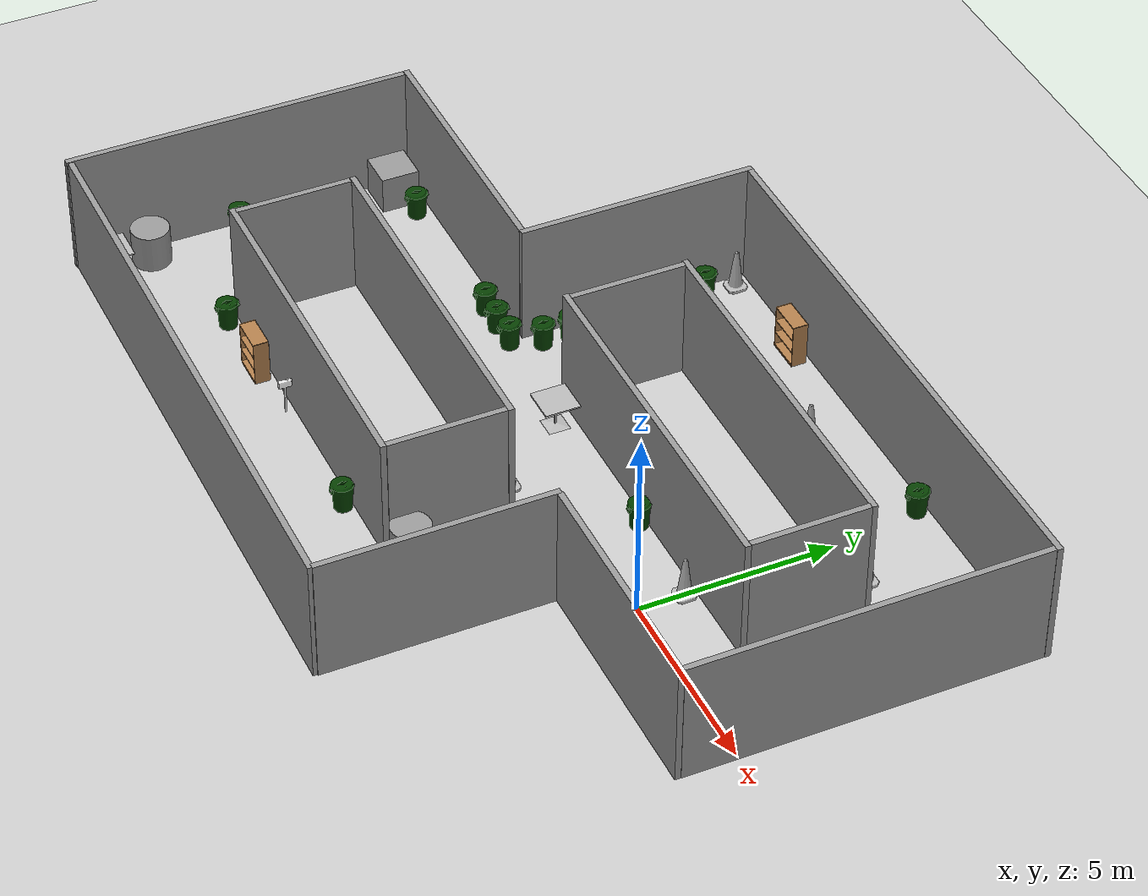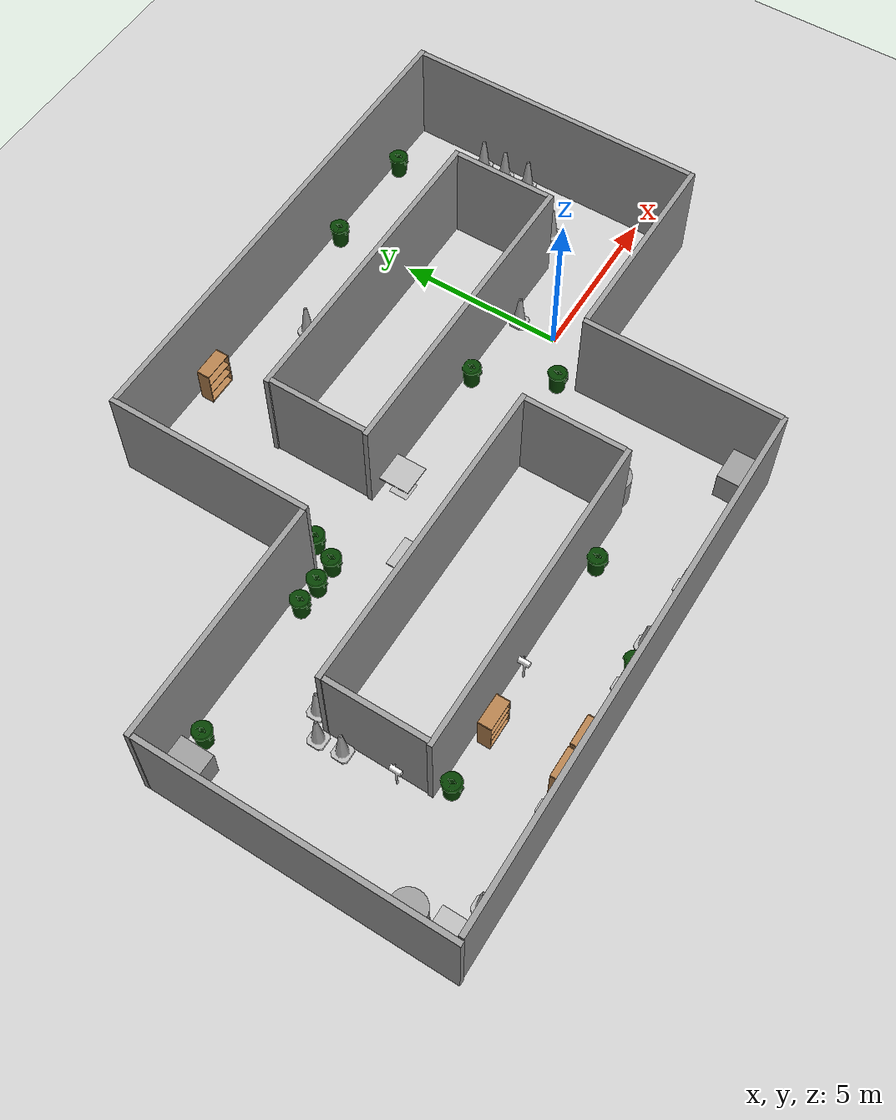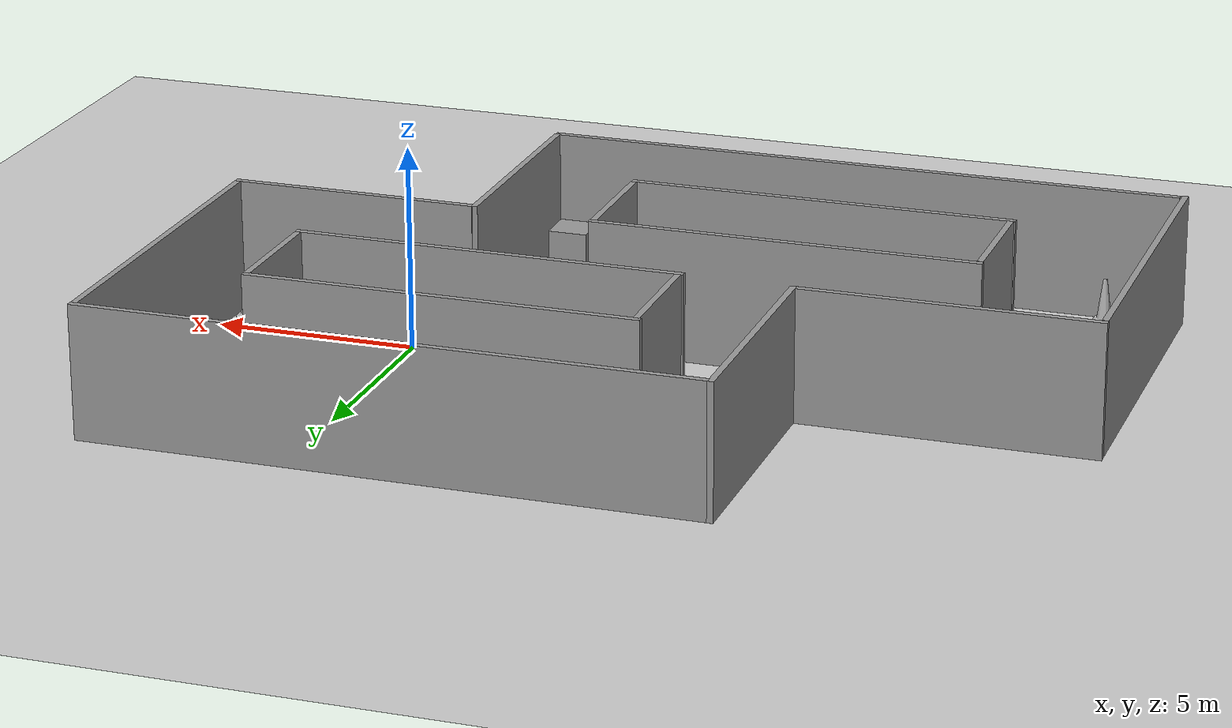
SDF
<sdf version="1.6">
 <world name="default">
  <light name="sun" type="directional">
   <pose>0 0 10 0 -0 0</pose>
   <diffuse>0.8 0.8 0.8 1</diffuse>
   <specular>0.2 0.2 0.2 1</specular>
   <attenuation>
    <range>1000</range>
    <constant>0.9</constant>
    <linear>0.01</linear>
    <quadratic>0.001</quadratic>
   </attenuation>
   <direction>-0.5 0.1 -0.9</direction>
  </light>
  <model name="ground_plane">
   <static>1</static>
   <link name="link">
    <collision name="collision">
     <geometry><plane><normal>0 0 1</normal><size>100 100</size></plane></geometry>
     <surface>
      <contact><collide_bitmask>65535</collide_bitmask></contact>
      <friction><ode><mu>100</mu><mu2>50</mu2></ode></friction>
     </surface>
    </collision>
    <visual name="visual">
     <cast_shadows>0</cast_shadows>
     <geometry><plane><normal>0 0 1</normal><size>100 100</size></plane></geometry>
     <material>
      <script><uri>file://media/materials/scripts/gazebo.material</uri><name>Gazebo/Grey</name></script>
     </material>
    </visual>
   </link>
  </model>
  <gravity>0 0 -9.8</gravity>
  <magnetic_field>6e-06 2.3e-05 -4.2e-05</magnetic_field>
  <atmosphere type="adiabatic"/>
  <physics name="default_physics" default="0" type="ode">
   <max_step_size>0.001</max_step_size>
   <real_time_factor>1</real_time_factor>
   <real_time_update_rate>1000</real_time_update_rate>
  </physics>
  <scene><ambient>0.4 0.4 0.4 1</ambient><background>0.7 0.7 0.7 1</background><shadows>1</shadows></scene>
  <audio><device>default</device></audio>
  <spherical_coordinates>
   <surface_model>EARTH_WGS84</surface_model>
   <latitude_deg>0</latitude_deg>
   <longitude_deg>0</longitude_deg>
   <elevation>0</elevation>
   <heading_deg>0</heading_deg>
  </spherical_coordinates>
  <model name="corridor_new_2_obs">
   <link name="link_0">
    <inertial>
     <mass>1</mass>
     <inertia>
      <ixx>0.166667</ixx>
      <ixy>0</ixy>
      <ixz>0</ixz>
      <iyy>0.166667</iyy>
      <iyz>0</iyz>
      <izz>0.166667</izz>
     </inertia>
    </inertial>
    <pose>5.27739 -6.22529 0.46 0 -0 0</pose>
    <visual name="visual">
     <geometry><box><size>1 1 1</size></box></geometry>
     <material>
      <lighting>1</lighting>
      <script><uri>file://media/materials/scripts/gazebo.material</uri><name>Gazebo/Grey</name></script>
     </material>
    </visual>
    <collision name="collision">
     <geometry><box><size>1 1 1</size></box></geometry>
     <surface>
      <friction>
       <ode><mu>1</mu><mu2>1</mu2><fdir1>0 0 0</fdir1><slip1>0</slip1><slip2>0</slip2></ode>
       <torsional>
        <coefficient>1</coefficient>
        <patch_radius>0</patch_radius>
        <surface_radius>0</surface_radius>
        <use_patch_radius>1</use_patch_radius>
        <ode><slip>0</slip></ode>
       </torsional>
      </friction>
      <bounce><restitution_coefficient>0</restitution_coefficient><threshold>1e+06</threshold></bounce>
      <contact>
       <collide_without_contact>0</collide_without_contact>
       <collide_without_contact_bitmask>1</collide_without_contact_bitmask>
       <collide_bitmask>1</collide_bitmask>
       <ode>
        <soft_cfm>0</soft_cfm>
        <soft_erp>0.2</soft_erp>
        <kp>1e+13</kp>
        <kd>1</kd>
        <max_vel>0.01</max_vel>
        <min_depth>0</min_depth>
       </ode>
       <bullet>
        <split_impulse>1</split_impulse>
        <split_impulse_penetration_threshold>-0.01</split_impulse_penetration_threshold>
        <soft_cfm>0</soft_cfm>
        <soft_erp>0.2</soft_erp>
        <kp>1e+13</kp>
        <kd>1</kd>
       </bullet>
      </contact>
     </surface>
    </collision>
   </link>
   <link name="link_2">
    <inertial>
     <mass>1</mass>
     <inertia><ixx>0.145833</ixx><ixy>0</ixy><ixz>0</ixz><iyy>0.145833</iyy><iyz>0</iyz><izz>0.125</izz></inertia>
    </inertial>
    <pose>3.2952 -3.37132 0.46 0 -0 0</pose>
    <visual name="visual">
     <geometry><cylinder><radius>0.5</radius><length>1</length></cylinder></geometry>
     <material>
      <lighting>1</lighting>
      <script><uri>file://media/materials/scripts/gazebo.material</uri><name>Gazebo/Grey</name></script>
     </material>
    </visual>
    <collision name="collision">
     <geometry><cylinder><radius>0.5</radius><length>1</length></cylinder></geometry>
     <surface>
      <friction>
       <ode><mu>1</mu><mu2>1</mu2><fdir1>0 0 0</fdir1><slip1>0</slip1><slip2>0</slip2></ode>
       <torsional>
        <coefficient>1</coefficient>
        <patch_radius>0</patch_radius>
        <surface_radius>0</surface_radius>
        <use_patch_radius>1</use_patch_radius>
        <ode><slip>0</slip></ode>
       </torsional>
      </friction>
      <bounce><restitution_coefficient>0</restitution_coefficient><threshold>1e+06</threshold></bounce>
      <contact>
       <collide_without_contact>0</collide_without_contact>
       <collide_without_contact_bitmask>1</collide_without_contact_bitmask>
       <collide_bitmask>1</collide_bitmask>
       <ode>
        <soft_cfm>0</soft_cfm>
        <soft_erp>0.2</soft_erp>
        <kp>1e+13</kp>
        <kd>1</kd>
        <max_vel>0.01</max_vel>
        <min_depth>0</min_depth>
       </ode>
       <bullet>
        <split_impulse>1</split_impulse>
        <split_impulse_penetration_threshold>-0.01</split_impulse_penetration_threshold>
        <soft_cfm>0</soft_cfm>
        <soft_erp>0.2</soft_erp>
        <kp>1e+13</kp>
        <kd>1</kd>
       </bullet>
      </contact>
     </surface>
    </collision>
   </link>
   <link name="link_3">
    <inertial>
     <mass>1</mass>
     <inertia><ixx>0.145833</ixx><ixy>0</ixy><ixz>0</ixz><iyy>0.145833</iyy><iyz>0</iyz><izz>0.125</izz></inertia>
    </inertial>
    <pose>-9.50964 -5.04997 0.46 0 -0 0</pose>
    <visual name="visual">
     <geometry><cylinder><radius>0.5</radius><length>1</length></cylinder></geometry>
     <material>
      <lighting>1</lighting>
      <script><uri>file://media/materials/scripts/gazebo.material</uri><name>Gazebo/Grey</name></script>
     </material>
    </visual>
    <collision name="collision">
     <geometry><cylinder><radius>0.5</radius><length>1</length></cylinder></geometry>
     <surface>
      <friction>
       <ode><mu>1</mu><mu2>1</mu2><fdir1>0 0 0</fdir1><slip1>0</slip1><slip2>0</slip2></ode>
       <torsional>
        <coefficient>1</coefficient>
        <patch_radius>0</patch_radius>
        <surface_radius>0</surface_radius>
        <use_patch_radius>1</use_patch_radius>
        <ode><slip>0</slip></ode>
       </torsional>
      </friction>
      <bounce><restitution_coefficient>0</restitution_coefficient><threshold>1e+06</threshold></bounce>
      <contact>
       <collide_without_contact>0</collide_without_contact>
       <collide_without_contact_bitmask>1</collide_without_contact_bitmask>
       <collide_bitmask>1</collide_bitmask>
       <ode>
        <soft_cfm>0</soft_cfm>
        <soft_erp>0.2</soft_erp>
        <kp>1e+13</kp>
        <kd>1</kd>
        <max_vel>0.01</max_vel>
        <min_depth>0</min_depth>
       </ode>
       <bullet>
        <split_impulse>1</split_impulse>
        <split_impulse_penetration_threshold>-0.01</split_impulse_penetration_threshold>
        <soft_cfm>0</soft_cfm>
        <soft_erp>0.2</soft_erp>
        <kp>1e+13</kp>
        <kd>1</kd>
       </bullet>
      </contact>
     </surface>
    </collision>
   </link>
   <link name="link_4">
    <inertial>
     <mass>1</mass>
     <inertia>
      <ixx>0.166667</ixx>
      <ixy>0</ixy>
      <ixz>0</ixz>
      <iyy>0.166667</iyy>
      <iyz>0</iyz>
      <izz>0.166667</izz>
     </inertia>
    </inertial>
    <pose>-9.38797 1.48332 0.46 0 -0 0</pose>
    <visual name="visual">
     <geometry><box><size>1 1 1</size></box></geometry>
     <material>
      <lighting>1</lighting>
      <script><uri>file://media/materials/scripts/gazebo.material</uri><name>Gazebo/Grey</name></script>
     </material>
    </visual>
    <collision name="collision">
     <geometry><box><size>1 1 1</size></box></geometry>
     <surface>
      <friction>
       <ode><mu>1</mu><mu2>1</mu2><fdir1>0 0 0</fdir1><slip1>0</slip1><slip2>0</slip2></ode>
       <torsional>
        <coefficient>1</coefficient>
        <patch_radius>0</patch_radius>
        <surface_radius>0</surface_radius>
        <use_patch_radius>1</use_patch_radius>
        <ode><slip>0</slip></ode>
       </torsional>
      </friction>
      <bounce><restitution_coefficient>0</restitution_coefficient><threshold>1e+06</threshold></bounce>
      <contact>
       <collide_without_contact>0</collide_without_contact>
       <collide_without_contact_bitmask>1</collide_without_contact_bitmask>
       <collide_bitmask>1</collide_bitmask>
       <ode>
        <soft_cfm>0</soft_cfm>
        <soft_erp>0.2</soft_erp>
        <kp>1e+13</kp>
        <kd>1</kd>
        <max_vel>0.01</max_vel>
        <min_depth>0</min_depth>
       </ode>
       <bullet>
        <split_impulse>1</split_impulse>
        <split_impulse_penetration_threshold>-0.01</split_impulse_penetration_threshold>
        <soft_cfm>0</soft_cfm>
        <soft_erp>0.2</soft_erp>
        <kp>1e+13</kp>
        <kd>1</kd>
       </bullet>
      </contact>
     </surface>
    </collision>
   </link>
   <model name="corridor_new_2">
    <model name="corridor_new">
     <link name="link">
      <inertial>
       <mass>5.22432</mass>
       <inertia><ixx>41.4535</ixx><ixy>0</ixy><ixz>0</ixz><iyy>6.07737</iyy><iyz>0</iyz><izz>35.3971</izz></inertia>
      </inertial>
      <pose>0.389725 1.0005 1.37091 0 -0 0</pose>
      <visual name="visual">
       <geometry><box><size>0.155445 9.01562 3.733</size></box></geometry>
       <material>
        <script><name>Gazebo/Grey</name><uri>file://media/materials/scripts/gazebo.material</uri></script>
        <emissive>0 0 0 1</emissive>
       </material>
      </visual>
      <collision name="collision">
       <geometry><box><size>0.155445 9.01562 3.733</size></box></geometry>
       <surface>
        <friction>
         <ode><mu>1</mu><mu2>1</mu2><fdir1>0 0 0</fdir1><slip1>0</slip1><slip2>0</slip2></ode>
         <torsional>
          <coefficient>1</coefficient>
          <patch_radius>0</patch_radius>
          <surface_radius>0</surface_radius>
          <use_patch_radius>1</use_patch_radius>
          <ode><slip>0</slip></ode>
         </torsional>
        </friction>
        <bounce><restitution_coefficient>0</restitution_coefficient><threshold>1e+06</threshold></bounce>
        <contact>
         <collide_without_contact>0</collide_without_contact>
         <collide_without_contact_bitmask>1</collide_without_contact_bitmask>
         <collide_bitmask>1</collide_bitmask>
         <ode>
          <soft_cfm>0</soft_cfm>
          <soft_erp>0.2</soft_erp>
          <kp>1e+13</kp>
          <kd>1</kd>
          <max_vel>0.01</max_vel>
          <min_depth>0</min_depth>
         </ode>
         <bullet>
          <split_impulse>1</split_impulse>
          <split_impulse_penetration_threshold>-0.01</split_impulse_penetration_threshold>
          <soft_cfm>0</soft_cfm>
          <soft_erp>0.2</soft_erp>
          <kp>1e+13</kp>
          <kd>1</kd>
         </bullet>
        </contact>
       </surface>
      </collision>
     </link>
     <link name="link_clone">
      <inertial>
       <mass>8.67159</mass>
       <inertia><ixx>171.895</ixx><ixy>0</ixy><ixz>0</ixz><iyy>10.0876</iyy><iyz>0</iyz><izz>161.843</izz></inertia>
      </inertial>
      <pose>-7.00537 5.58222 1.37085 0 -1e-05 -1.57076</pose>
      <visual name="visual">
       <geometry><box><size>0.155445 14.9646 3.733</size></box></geometry>
       <material>
        <script><name>Gazebo/Grey</name><uri>file://media/materials/scripts/gazebo.material</uri></script>
        <shader type="pixel"/>
        <emissive>0 0 0 1</emissive>
       </material>
      </visual>
      <collision name="collision">
       <geometry><box><size>0.155445 14.9646 3.733</size></box></geometry>
       <surface>
        <friction>
         <ode><mu>1</mu><mu2>1</mu2><fdir1>0 0 0</fdir1><slip1>0</slip1><slip2>0</slip2></ode>
         <torsional>
          <coefficient>1</coefficient>
          <patch_radius>0</patch_radius>
          <surface_radius>0</surface_radius>
          <use_patch_radius>1</use_patch_radius>
          <ode><slip>0</slip></ode>
         </torsional>
        </friction>
        <bounce><restitution_coefficient>0</restitution_coefficient><threshold>1e+06</threshold></bounce>
        <contact>
         <collide_without_contact>0</collide_without_contact>
         <collide_without_contact_bitmask>1</collide_without_contact_bitmask>
         <collide_bitmask>1</collide_bitmask>
         <ode>
          <soft_cfm>0</soft_cfm>
          <soft_erp>0.2</soft_erp>
          <kp>1e+13</kp>
          <kd>1</kd>
          <max_vel>0.01</max_vel>
          <min_depth>0</min_depth>
         </ode>
         <bullet>
          <split_impulse>1</split_impulse>
          <split_impulse_penetration_threshold>-0.01</split_impulse_penetration_threshold>
          <soft_cfm>0</soft_cfm>
          <soft_erp>0.2</soft_erp>
          <kp>1e+13</kp>
          <kd>1</kd>
         </bullet>
        </contact>
       </surface>
      </collision>
     </link>
     <link name="link_clone_0">
      <inertial>
       <mass>1.73165</mass>
       <inertia><ixx>3.29955</ixx><ixy>0</ixy><ixz>0</ixz><iyy>2.0144</iyy><iyz>0</iyz><izz>1.29212</izz></inertia>
      </inertial>
      <pose>-2.47833 1.00389 1.3709 -1e-05 0 0</pose>
      <visual name="visual">
       <geometry><box><size>0.155445 2.98831 3.733</size></box></geometry>
       <material>
        <script><name>Gazebo/Grey</name><uri>file://media/materials/scripts/gazebo.material</uri></script>
        <shader type="pixel"/>
        <emissive>0 0 0 1</emissive>
       </material>
      </visual>
      <collision name="collision">
       <geometry><box><size>0.155445 2.98831 3.733</size></box></geometry>
       <surface>
        <friction>
         <ode><mu>1</mu><mu2>1</mu2><fdir1>0 0 0</fdir1><slip1>0</slip1><slip2>0</slip2></ode>
         <torsional>
          <coefficient>1</coefficient>
          <patch_radius>0</patch_radius>
          <surface_radius>0</surface_radius>
          <use_patch_radius>1</use_patch_radius>
          <ode><slip>0</slip></ode>
         </torsional>
        </friction>
        <bounce><restitution_coefficient>0</restitution_coefficient><threshold>1e+06</threshold></bounce>
        <contact>
         <collide_without_contact>0</collide_without_contact>
         <collide_without_contact_bitmask>1</collide_without_contact_bitmask>
         <collide_bitmask>1</collide_bitmask>
         <ode>
          <soft_cfm>0</soft_cfm>
          <soft_erp>0.2</soft_erp>
          <kp>1e+13</kp>
          <kd>1</kd>
          <max_vel>0.01</max_vel>
          <min_depth>0</min_depth>
         </ode>
         <bullet>
          <split_impulse>1</split_impulse>
          <split_impulse_penetration_threshold>-0.01</split_impulse_penetration_threshold>
          <soft_cfm>0</soft_cfm>
          <soft_erp>0.2</soft_erp>
          <kp>1e+13</kp>
          <kd>1</kd>
         </bullet>
        </contact>
       </surface>
      </collision>
     </link>
     <link name="link_clone_0_clone">
      <inertial>
       <mass>1.73165</mass>
       <inertia><ixx>3.29955</ixx><ixy>0</ixy><ixz>0</ixz><iyy>2.0144</iyy><iyz>0</iyz><izz>1.29212</izz></inertia>
      </inertial>
      <pose>-11.8317 1.00201 1.37089 -2e-05 0 0</pose>
      <visual name="visual">
       <geometry><box><size>0.155445 2.98831 3.733</size></box></geometry>
       <material>
        <script><name>Gazebo/Grey</name><uri>file://media/materials/scripts/gazebo.material</uri></script>
        <shader type="pixel"/>
        <emissive>0 0 0 1</emissive>
       </material>
      </visual>
      <collision name="collision">
       <geometry><box><size>0.155445 2.98831 3.733</size></box></geometry>
       <surface>
        <friction>
         <ode><mu>1</mu><mu2>1</mu2><fdir1>0 0 0</fdir1><slip1>0</slip1><slip2>0</slip2></ode>
         <torsional>
          <coefficient>1</coefficient>
          <patch_radius>0</patch_radius>
          <surface_radius>0</surface_radius>
          <use_patch_radius>1</use_patch_radius>
          <ode><slip>0</slip></ode>
         </torsional>
        </friction>
        <bounce><restitution_coefficient>0</restitution_coefficient><threshold>1e+06</threshold></bounce>
        <contact>
         <collide_without_contact>0</collide_without_contact>
         <collide_without_contact_bitmask>1</collide_without_contact_bitmask>
         <collide_bitmask>1</collide_bitmask>
         <ode>
          <soft_cfm>0</soft_cfm>
          <soft_erp>0.2</soft_erp>
          <kp>1e+13</kp>
          <kd>1</kd>
          <max_vel>0.01</max_vel>
          <min_depth>0</min_depth>
         </ode>
         <bullet>
          <split_impulse>1</split_impulse>
          <split_impulse_penetration_threshold>-0.01</split_impulse_penetration_threshold>
          <soft_cfm>0</soft_cfm>
          <soft_erp>0.2</soft_erp>
          <kp>1e+13</kp>
          <kd>1</kd>
         </bullet>
        </contact>
       </surface>
      </collision>
     </link>
     <link name="link_clone_0_clone_0">
      <inertial>
       <mass>1.73165</mass>
       <inertia><ixx>3.29955</ixx><ixy>0</ixy><ixz>0</ixz><iyy>2.0144</iyy><iyz>0</iyz><izz>1.29212</izz></inertia>
      </inertial>
      <pose>-8.76241 -4.9873 1.37095 -2e-05 0 0</pose>
      <visual name="visual">
       <geometry><box><size>0.155445 2.98831 3.733</size></box></geometry>
       <material>
        <script><name>Gazebo/Grey</name><uri>file://media/materials/scripts/gazebo.material</uri></script>
        <shader type="pixel"/>
       </material>
      </visual>
      <collision name="collision">
       <geometry><box><size>0.155445 2.98831 3.733</size></box></geometry>
       <surface>
        <friction>
         <ode><mu>1</mu><mu2>1</mu2><fdir1>0 0 0</fdir1><slip1>0</slip1><slip2>0</slip2></ode>
         <torsional>
          <coefficient>1</coefficient>
          <patch_radius>0</patch_radius>
          <surface_radius>0</surface_radius>
          <use_patch_radius>1</use_patch_radius>
          <ode><slip>0</slip></ode>
         </torsional>
        </friction>
        <bounce><restitution_coefficient>0</restitution_coefficient><threshold>1e+06</threshold></bounce>
        <contact>
         <collide_without_contact>0</collide_without_contact>
         <collide_without_contact_bitmask>1</collide_without_contact_bitmask>
         <collide_bitmask>1</collide_bitmask>
         <ode>
          <soft_cfm>0</soft_cfm>
          <soft_erp>0.2</soft_erp>
          <kp>1e+13</kp>
          <kd>1</kd>
          <max_vel>0.01</max_vel>
          <min_depth>0</min_depth>
         </ode>
         <bullet>
          <split_impulse>1</split_impulse>
          <split_impulse_penetration_threshold>-0.01</split_impulse_penetration_threshold>
          <soft_cfm>0</soft_cfm>
          <soft_erp>0.2</soft_erp>
          <kp>1e+13</kp>
          <kd>1</kd>
         </bullet>
        </contact>
       </surface>
      </collision>
     </link>
     <link name="link_clone_0_clone_0_clone">
      <inertial>
       <mass>1.73165</mass>
       <inertia><ixx>3.29955</ixx><ixy>0</ixy><ixz>0</ixz><iyy>2.0144</iyy><iyz>0</iyz><izz>1.29212</izz></inertia>
      </inertial>
      <pose>-18.1425 -5.00451 1.371 -3e-05 0 0</pose>
      <visual name="visual">
       <geometry><box><size>0.155445 2.98831 3.733</size></box></geometry>
       <material>
        <script><name>Gazebo/Grey</name><uri>file://media/materials/scripts/gazebo.material</uri></script>
        <shader type="pixel"/>
       </material>
      </visual>
      <collision name="collision">
       <geometry><box><size>0.155445 2.98831 3.733</size></box></geometry>
       <surface>
        <friction>
         <ode><mu>1</mu><mu2>1</mu2><fdir1>0 0 0</fdir1><slip1>0</slip1><slip2>0</slip2></ode>
         <torsional>
          <coefficient>1</coefficient>
          <patch_radius>0</patch_radius>
          <surface_radius>0</surface_radius>
          <use_patch_radius>1</use_patch_radius>
          <ode><slip>0</slip></ode>
         </torsional>
        </friction>
        <bounce><restitution_coefficient>0</restitution_coefficient><threshold>1e+06</threshold></bounce>
        <contact>
         <collide_without_contact>0</collide_without_contact>
         <collide_without_contact_bitmask>1</collide_without_contact_bitmask>
         <collide_bitmask>1</collide_bitmask>
         <ode>
          <soft_cfm>0</soft_cfm>
          <soft_erp>0.2</soft_erp>
          <kp>1e+13</kp>
          <kd>1</kd>
          <max_vel>0.01</max_vel>
          <min_depth>0</min_depth>
         </ode>
         <bullet>
          <split_impulse>1</split_impulse>
          <split_impulse_penetration_threshold>-0.01</split_impulse_penetration_threshold>
          <soft_cfm>0</soft_cfm>
          <soft_erp>0.2</soft_erp>
          <kp>1e+13</kp>
          <kd>1</kd>
         </bullet>
        </contact>
       </surface>
      </collision>
     </link>
     <link name="link_clone_1">
      <inertial>
       <mass>3.44824</mass>
       <inertia><ixx>14.1795</ixx><ixy>0</ixy><ixz>0</ixz><iyy>4.01129</iyy><iyz>0</iyz><izz>10.1821</izz></inertia>
      </inertial>
      <pose>-5.73661 -6.50426 1.37098 -1e-05 -0 0</pose>
      <visual name="visual">
       <geometry><box><size>0.155445 5.95062 3.733</size></box></geometry>
       <material>
        <script><name>Gazebo/Grey</name><uri>file://media/materials/scripts/gazebo.material</uri></script>
        <shader type="pixel"/>
       </material>
      </visual>
      <collision name="collision">
       <geometry><box><size>0.155445 5.95062 3.733</size></box></geometry>
       <surface>
        <friction>
         <ode><mu>1</mu><mu2>1</mu2><fdir1>0 0 0</fdir1><slip1>0</slip1><slip2>0</slip2></ode>
         <torsional>
          <coefficient>1</coefficient>
          <patch_radius>0</patch_radius>
          <surface_radius>0</surface_radius>
          <use_patch_radius>1</use_patch_radius>
          <ode><slip>0</slip></ode>
         </torsional>
        </friction>
        <bounce><restitution_coefficient>0</restitution_coefficient><threshold>1e+06</threshold></bounce>
        <contact>
         <collide_without_contact>0</collide_without_contact>
         <collide_without_contact_bitmask>1</collide_without_contact_bitmask>
         <collide_bitmask>1</collide_bitmask>
         <ode>
          <soft_cfm>0</soft_cfm>
          <soft_erp>0.2</soft_erp>
          <kp>1e+13</kp>
          <kd>1</kd>
          <max_vel>0.01</max_vel>
          <min_depth>0</min_depth>
         </ode>
         <bullet>
          <split_impulse>1</split_impulse>
          <split_impulse_penetration_threshold>-0.01</split_impulse_penetration_threshold>
          <soft_cfm>0</soft_cfm>
          <soft_erp>0.2</soft_erp>
          <kp>1e+13</kp>
          <kd>1</kd>
         </bullet>
        </contact>
       </surface>
      </collision>
     </link>
     <link name="link_clone_2">
      <inertial>
       <mass>5.22432</mass>
       <inertia><ixx>41.4535</ixx><ixy>0</ixy><ixz>0</ixz><iyy>6.07737</iyy><iyz>0</iyz><izz>35.3971</izz></inertia>
      </inertial>
      <pose>-21.7001 -5.10431 1.37096 -1e-05 0 0</pose>
      <visual name="visual">
       <geometry><box><size>0.155445 9.01562 3.733</size></box></geometry>
       <material>
        <script><name>Gazebo/Grey</name><uri>file://media/materials/scripts/gazebo.material</uri></script>
        <shader type="pixel"/>
        <emissive>0 0 0 1</emissive>
       </material>
      </visual>
      <collision name="collision">
       <geometry><box><size>0.155445 9.01562 3.733</size></box></geometry>
       <surface>
        <friction>
         <ode><mu>1</mu><mu2>1</mu2><fdir1>0 0 0</fdir1><slip1>0</slip1><slip2>0</slip2></ode>
         <torsional>
          <coefficient>1</coefficient>
          <patch_radius>0</patch_radius>
          <surface_radius>0</surface_radius>
          <use_patch_radius>1</use_patch_radius>
          <ode><slip>0</slip></ode>
         </torsional>
        </friction>
        <bounce><restitution_coefficient>0</restitution_coefficient><threshold>1e+06</threshold></bounce>
        <contact>
         <collide_without_contact>0</collide_without_contact>
         <collide_without_contact_bitmask>1</collide_without_contact_bitmask>
         <collide_bitmask>1</collide_bitmask>
         <ode>
          <soft_cfm>0</soft_cfm>
          <soft_erp>0.2</soft_erp>
          <kp>1e+13</kp>
          <kd>1</kd>
          <max_vel>0.01</max_vel>
          <min_depth>0</min_depth>
         </ode>
         <bullet>
          <split_impulse>1</split_impulse>
          <split_impulse_penetration_threshold>-0.01</split_impulse_penetration_threshold>
          <soft_cfm>0</soft_cfm>
          <soft_erp>0.2</soft_erp>
          <kp>1e+13</kp>
          <kd>1</kd>
         </bullet>
        </contact>
       </surface>
      </collision>
     </link>
     <link name="link_clone_3">
      <inertial>
       <mass>3.60563</mass>
       <inertia><ixx>15.8201</ixx><ixy>0</ixy><ixz>0</ixz><iyy>4.19438</iyy><iyz>0</iyz><izz>11.6403</izz></inertia>
      </inertial>
      <pose>-14.5512 2.55131 1.37088 -1e-05 0 0</pose>
      <visual name="visual">
       <geometry><box><size>0.155445 6.22223 3.733</size></box></geometry>
       <material>
        <script><name>Gazebo/Grey</name><uri>file://media/materials/scripts/gazebo.material</uri></script>
        <shader type="pixel"/>
        <emissive>0 0 0 1</emissive>
       </material>
      </visual>
      <collision name="collision">
       <geometry><box><size>0.155445 6.22223 3.733</size></box></geometry>
       <surface>
        <friction>
         <ode><mu>1</mu><mu2>1</mu2><fdir1>0 0 0</fdir1><slip1>0</slip1><slip2>0</slip2></ode>
         <torsional>
          <coefficient>1</coefficient>
          <patch_radius>0</patch_radius>
          <surface_radius>0</surface_radius>
          <use_patch_radius>1</use_patch_radius>
          <ode><slip>0</slip></ode>
         </torsional>
        </friction>
        <bounce><restitution_coefficient>0</restitution_coefficient><threshold>1e+06</threshold></bounce>
        <contact>
         <collide_without_contact>0</collide_without_contact>
         <collide_without_contact_bitmask>1</collide_without_contact_bitmask>
         <collide_bitmask>1</collide_bitmask>
         <ode>
          <soft_cfm>0</soft_cfm>
          <soft_erp>0.2</soft_erp>
          <kp>1e+13</kp>
          <kd>1</kd>
          <max_vel>0.01</max_vel>
          <min_depth>0</min_depth>
         </ode>
         <bullet>
          <split_impulse>1</split_impulse>
          <split_impulse_penetration_threshold>-0.01</split_impulse_penetration_threshold>
          <soft_cfm>0</soft_cfm>
          <soft_erp>0.2</soft_erp>
          <kp>1e+13</kp>
          <kd>1</kd>
         </bullet>
        </contact>
       </surface>
      </collision>
     </link>
     <link name="link_clone_clone">
      <inertial>
       <mass>5.53631</mass>
       <inertia><ixx>48.5418</ixx><ixy>0</ixy><ixz>0</ixz><iyy>6.44032</iyy><iyz>0</iyz><izz>42.1237</izz></inertia>
      </inertial>
      <pose>-7.178 2.55784 1.37082 -0 -2e-05 -1.57076</pose>
      <visual name="visual">
       <geometry><box><size>0.155445 9.55403 3.733</size></box></geometry>
       <material>
        <script><name>Gazebo/Grey</name><uri>file://media/materials/scripts/gazebo.material</uri></script>
        <shader type="pixel"/>
        <emissive>0 0 0 1</emissive>
       </material>
      </visual>
      <collision name="collision">
       <geometry><box><size>0.155445 9.55403 3.733</size></box></geometry>
       <surface>
        <friction>
         <ode><mu>1</mu><mu2>1</mu2><fdir1>0 0 0</fdir1><slip1>0</slip1><slip2>0</slip2></ode>
         <torsional>
          <coefficient>1</coefficient>
          <patch_radius>0</patch_radius>
          <surface_radius>0</surface_radius>
          <use_patch_radius>1</use_patch_radius>
          <ode><slip>0</slip></ode>
         </torsional>
        </friction>
        <bounce><restitution_coefficient>0</restitution_coefficient><threshold>1e+06</threshold></bounce>
        <contact>
         <collide_without_contact>0</collide_without_contact>
         <collide_without_contact_bitmask>1</collide_without_contact_bitmask>
         <collide_bitmask>1</collide_bitmask>
         <ode>
          <soft_cfm>0</soft_cfm>
          <soft_erp>0.2</soft_erp>
          <kp>1e+13</kp>
          <kd>1</kd>
          <max_vel>0.01</max_vel>
          <min_depth>0</min_depth>
         </ode>
         <bullet>
          <split_impulse>1</split_impulse>
          <split_impulse_penetration_threshold>-0.01</split_impulse_penetration_threshold>
          <soft_cfm>0</soft_cfm>
          <soft_erp>0.2</soft_erp>
          <kp>1e+13</kp>
          <kd>1</kd>
         </bullet>
        </contact>
       </surface>
      </collision>
     </link>
     <link name="link_clone_clone_clone">
      <inertial>
       <mass>5.53631</mass>
       <inertia><ixx>48.5418</ixx><ixy>0</ixy><ixz>0</ixz><iyy>6.44032</iyy><iyz>0</iyz><izz>42.1237</izz></inertia>
      </inertial>
      <pose>-7.17302 -0.570724 1.37083 -0 -3e-05 -1.57076</pose>
      <visual name="visual">
       <geometry><box><size>0.155445 9.55403 3.733</size></box></geometry>
       <material>
        <script><name>Gazebo/Grey</name><uri>file://media/materials/scripts/gazebo.material</uri></script>
        <shader type="pixel"/>
       </material>
      </visual>
      <collision name="collision">
       <geometry><box><size>0.155445 9.55403 3.733</size></box></geometry>
       <surface>
        <friction>
         <ode><mu>1</mu><mu2>1</mu2><fdir1>0 0 0</fdir1><slip1>0</slip1><slip2>0</slip2></ode>
         <torsional>
          <coefficient>1</coefficient>
          <patch_radius>0</patch_radius>
          <surface_radius>0</surface_radius>
          <use_patch_radius>1</use_patch_radius>
          <ode><slip>0</slip></ode>
         </torsional>
        </friction>
        <bounce><restitution_coefficient>0</restitution_coefficient><threshold>1e+06</threshold></bounce>
        <contact>
         <collide_without_contact>0</collide_without_contact>
         <collide_without_contact_bitmask>1</collide_without_contact_bitmask>
         <collide_bitmask>1</collide_bitmask>
         <ode>
          <soft_cfm>0</soft_cfm>
          <soft_erp>0.2</soft_erp>
          <kp>1e+13</kp>
          <kd>1</kd>
          <max_vel>0.01</max_vel>
          <min_depth>0</min_depth>
         </ode>
         <bullet>
          <split_impulse>1</split_impulse>
          <split_impulse_penetration_threshold>-0.01</split_impulse_penetration_threshold>
          <soft_cfm>0</soft_cfm>
          <soft_erp>0.2</soft_erp>
          <kp>1e+13</kp>
          <kd>1</kd>
         </bullet>
        </contact>
       </surface>
      </collision>
     </link>
     <link name="link_clone_clone_clone_0">
      <inertial>
       <mass>5.53631</mass>
       <inertia><ixx>48.5418</ixx><ixy>0</ixy><ixz>0</ixz><iyy>6.44032</iyy><iyz>0</iyz><izz>42.1237</izz></inertia>
      </inertial>
      <pose>-13.4523 -3.41595 1.37085 -0 -3e-05 -1.57076</pose>
      <visual name="visual">
       <geometry><box><size>0.155445 9.55403 3.733</size></box></geometry>
       <material>
        <script><name>Gazebo/Grey</name><uri>file://media/materials/scripts/gazebo.material</uri></script>
        <shader type="pixel"/>
       </material>
      </visual>
      <collision name="collision">
       <geometry><box><size>0.155445 9.55403 3.733</size></box></geometry>
       <surface>
        <friction>
         <ode><mu>1</mu><mu2>1</mu2><fdir1>0 0 0</fdir1><slip1>0</slip1><slip2>0</slip2></ode>
         <torsional>
          <coefficient>1</coefficient>
          <patch_radius>0</patch_radius>
          <surface_radius>0</surface_radius>
          <use_patch_radius>1</use_patch_radius>
          <ode><slip>0</slip></ode>
         </torsional>
        </friction>
        <bounce><restitution_coefficient>0</restitution_coefficient><threshold>1e+06</threshold></bounce>
        <contact>
         <collide_without_contact>0</collide_without_contact>
         <collide_without_contact_bitmask>1</collide_without_contact_bitmask>
         <collide_bitmask>1</collide_bitmask>
         <ode>
          <soft_cfm>0</soft_cfm>
          <soft_erp>0.2</soft_erp>
          <kp>1e+13</kp>
          <kd>1</kd>
          <max_vel>0.01</max_vel>
          <min_depth>0</min_depth>
         </ode>
         <bullet>
          <split_impulse>1</split_impulse>
          <split_impulse_penetration_threshold>-0.01</split_impulse_penetration_threshold>
          <soft_cfm>0</soft_cfm>
          <soft_erp>0.2</soft_erp>
          <kp>1e+13</kp>
          <kd>1</kd>
         </bullet>
        </contact>
       </surface>
      </collision>
     </link>
     <link name="link_clone_clone_clone_0_clone">
      <inertial>
       <mass>5.53631</mass>
       <inertia><ixx>48.5418</ixx><ixy>0</ixy><ixz>0</ixz><iyy>6.44032</iyy><iyz>0</iyz><izz>42.1237</izz></inertia>
      </inertial>
      <pose>-13.4756 -6.55755 1.37091 0 -4e-05 -1.57076</pose>
      <visual name="visual">
       <geometry><box><size>0.155445 9.55403 3.733</size></box></geometry>
       <material>
        <script><name>Gazebo/Grey</name><uri>file://media/materials/scripts/gazebo.material</uri></script>
        <shader type="pixel"/>
       </material>
      </visual>
      <collision name="collision">
       <geometry><box><size>0.155445 9.55403 3.733</size></box></geometry>
       <surface>
        <friction>
         <ode><mu>1</mu><mu2>1</mu2><fdir1>0 0 0</fdir1><slip1>0</slip1><slip2>0</slip2></ode>
         <torsional>
          <coefficient>1</coefficient>
          <patch_radius>0</patch_radius>
          <surface_radius>0</surface_radius>
          <use_patch_radius>1</use_patch_radius>
          <ode><slip>0</slip></ode>
         </torsional>
        </friction>
        <bounce><restitution_coefficient>0</restitution_coefficient><threshold>1e+06</threshold></bounce>
        <contact>
         <collide_without_contact>0</collide_without_contact>
         <collide_without_contact_bitmask>1</collide_without_contact_bitmask>
         <collide_bitmask>1</collide_bitmask>
         <ode>
          <soft_cfm>0</soft_cfm>
          <soft_erp>0.2</soft_erp>
          <kp>1e+13</kp>
          <kd>1</kd>
          <max_vel>0.01</max_vel>
          <min_depth>0</min_depth>
         </ode>
         <bullet>
          <split_impulse>1</split_impulse>
          <split_impulse_penetration_threshold>-0.01</split_impulse_penetration_threshold>
          <soft_cfm>0</soft_cfm>
          <soft_erp>0.2</soft_erp>
          <kp>1e+13</kp>
          <kd>1</kd>
         </bullet>
        </contact>
       </surface>
      </collision>
     </link>
     <link name="link_clone_clone_clone_0_clone_clone">
      <inertial>
       <mass>9.21687</mass>
       <inertia><ixx>205.017</ixx><ixy>0</ixy><ixz>0</ixz><iyy>10.7219</iyy><iyz>0</iyz><izz>194.332</izz></inertia>
      </inertial>
      <pose>-13.6388 -9.50846 1.371 0 -5e-05 -1.57076</pose>
      <visual name="visual">
       <geometry><box><size>0.155445 15.9056 3.733</size></box></geometry>
       <material>
        <script><name>Gazebo/Grey</name><uri>file://media/materials/scripts/gazebo.material</uri></script>
        <shader type="pixel"/>
       </material>
      </visual>
      <collision name="collision">
       <geometry><box><size>0.155445 15.9056 3.733</size></box></geometry>
       <surface>
        <friction>
         <ode><mu>1</mu><mu2>1</mu2><fdir1>0 0 0</fdir1><slip1>0</slip1><slip2>0</slip2></ode>
         <torsional>
          <coefficient>1</coefficient>
          <patch_radius>0</patch_radius>
          <surface_radius>0</surface_radius>
          <use_patch_radius>1</use_patch_radius>
          <ode><slip>0</slip></ode>
         </torsional>
        </friction>
        <bounce><restitution_coefficient>0</restitution_coefficient><threshold>1e+06</threshold></bounce>
        <contact>
         <collide_without_contact>0</collide_without_contact>
         <collide_without_contact_bitmask>1</collide_without_contact_bitmask>
         <collide_bitmask>1</collide_bitmask>
         <ode>
          <soft_cfm>0</soft_cfm>
          <soft_erp>0.2</soft_erp>
          <kp>1e+13</kp>
          <kd>1</kd>
          <max_vel>0.01</max_vel>
          <min_depth>0</min_depth>
         </ode>
         <bullet>
          <split_impulse>1</split_impulse>
          <split_impulse_penetration_threshold>-0.01</split_impulse_penetration_threshold>
          <soft_cfm>0</soft_cfm>
          <soft_erp>0.2</soft_erp>
          <kp>1e+13</kp>
          <kd>1</kd>
         </bullet>
        </contact>
       </surface>
      </collision>
     </link>
     <link name="link_clone_clone_clone_1">
      <inertial>
       <mass>4.15739</mass>
       <inertia><ixx>22.6605</ixx><ixy>0</ixy><ixz>0</ixz><iyy>4.83625</iyy><iyz>0</iyz><izz>17.841</izz></inertia>
      </inertial>
      <pose>-18.1948 -0.500264 1.37082 -0 -3e-05 -1.57076</pose>
      <visual name="visual">
       <geometry><box><size>0.155445 7.17444 3.733</size></box></geometry>
       <material>
        <script><name>Gazebo/Grey</name><uri>file://media/materials/scripts/gazebo.material</uri></script>
        <shader type="pixel"/>
        <emissive>0 0 0 1</emissive>
       </material>
      </visual>
      <collision name="collision">
       <geometry><box><size>0.155445 7.17444 3.733</size></box></geometry>
       <surface>
        <friction>
         <ode><mu>1</mu><mu2>1</mu2><fdir1>0 0 0</fdir1><slip1>0</slip1><slip2>0</slip2></ode>
         <torsional>
          <coefficient>1</coefficient>
          <patch_radius>0</patch_radius>
          <surface_radius>0</surface_radius>
          <use_patch_radius>1</use_patch_radius>
          <ode><slip>0</slip></ode>
         </torsional>
        </friction>
        <bounce><restitution_coefficient>0</restitution_coefficient><threshold>1e+06</threshold></bounce>
        <contact>
         <collide_without_contact>0</collide_without_contact>
         <collide_without_contact_bitmask>1</collide_without_contact_bitmask>
         <collide_bitmask>1</collide_bitmask>
         <ode>
          <soft_cfm>0</soft_cfm>
          <soft_erp>0.2</soft_erp>
          <kp>1e+13</kp>
          <kd>1</kd>
          <max_vel>0.01</max_vel>
          <min_depth>0</min_depth>
         </ode>
         <bullet>
          <split_impulse>1</split_impulse>
          <split_impulse_penetration_threshold>-0.01</split_impulse_penetration_threshold>
          <soft_cfm>0</soft_cfm>
          <soft_erp>0.2</soft_erp>
          <kp>1e+13</kp>
          <kd>1</kd>
         </bullet>
        </contact>
       </surface>
      </collision>
     </link>
     <link name="link_clone_clone_clone_clone">
      <inertial>
       <mass>3.55678</mass>
       <inertia><ixx>15.297</ixx><ixy>0</ixy><ixz>0</ixz><iyy>4.13756</iyy><iyz>0</iyz><izz>11.1738</izz></inertia>
      </inertial>
      <pose>-2.60693 -3.57842 1.37087 0 -4e-05 -1.57076</pose>
      <visual name="visual">
       <geometry><box><size>0.155445 6.13794 3.733</size></box></geometry>
       <material>
        <script><name>Gazebo/Grey</name><uri>file://media/materials/scripts/gazebo.material</uri></script>
        <shader type="pixel"/>
       </material>
      </visual>
      <collision name="collision">
       <geometry><box><size>0.155445 6.13794 3.733</size></box></geometry>
       <surface>
        <friction>
         <ode><mu>1</mu><mu2>1</mu2><fdir1>0 0 0</fdir1><slip1>0</slip1><slip2>0</slip2></ode>
         <torsional>
          <coefficient>1</coefficient>
          <patch_radius>0</patch_radius>
          <surface_radius>0</surface_radius>
          <use_patch_radius>1</use_patch_radius>
          <ode><slip>0</slip></ode>
         </torsional>
        </friction>
        <bounce><restitution_coefficient>0</restitution_coefficient><threshold>1e+06</threshold></bounce>
        <contact>
         <collide_without_contact>0</collide_without_contact>
         <collide_without_contact_bitmask>1</collide_without_contact_bitmask>
         <collide_bitmask>1</collide_bitmask>
         <ode>
          <soft_cfm>0</soft_cfm>
          <soft_erp>0.2</soft_erp>
          <kp>1e+13</kp>
          <kd>1</kd>
          <max_vel>0.01</max_vel>
          <min_depth>0</min_depth>
         </ode>
         <bullet>
          <split_impulse>1</split_impulse>
          <split_impulse_penetration_threshold>-0.01</split_impulse_penetration_threshold>
          <soft_cfm>0</soft_cfm>
          <soft_erp>0.2</soft_erp>
          <kp>1e+13</kp>
          <kd>1</kd>
         </bullet>
        </contact>
       </surface>
      </collision>
     </link>
     <static>0</static>
     <pose>-3e-06 0 0 0 -0 0</pose>
    </model>
    <joint name="link_JOINT_7" type="fixed">
     <parent>corridor_new::link</parent>
     <child>corridor_new::link_clone_clone_clone_clone</child>
     <physics>
      <ode><limit><cfm>0</cfm><erp>0.2</erp></limit><suspension><cfm>0</cfm><erp>0.2</erp></suspension></ode>
     </physics>
    </joint>
    <joint name="link_clone_0_JOINT_14" type="fixed">
     <parent>corridor_new::link_clone_0</parent>
     <child>corridor_new::link_clone_clone</child>
     <physics>
      <ode><limit><cfm>0</cfm><erp>0.2</erp></limit><suspension><cfm>0</cfm><erp>0.2</erp></suspension></ode>
     </physics>
    </joint>
    <joint name="link_clone_0_JOINT_22" type="fixed">
     <parent>corridor_new::link_clone_0</parent>
     <child>corridor_new::link</child>
     <physics>
      <ode><limit><cfm>0</cfm><erp>0.2</erp></limit><suspension><cfm>0</cfm><erp>0.2</erp></suspension></ode>
     </physics>
    </joint>
    <joint name="link_clone_0_clone_0_JOINT_10" type="fixed">
     <parent>corridor_new::link_clone_0_clone_0</parent>
     <child>corridor_new::link_clone_clone_clone_0</child>
     <physics>
      <ode><limit><cfm>0</cfm><erp>0.2</erp></limit><suspension><cfm>0</cfm><erp>0.2</erp></suspension></ode>
     </physics>
    </joint>
    <joint name="link_clone_0_clone_0_JOINT_17" type="fixed">
     <parent>corridor_new::link_clone_0_clone_0</parent>
     <child>corridor_new::link_clone_1</child>
     <physics>
      <ode><limit><cfm>0</cfm><erp>0.2</erp></limit><suspension><cfm>0</cfm><erp>0.2</erp></suspension></ode>
     </physics>
    </joint>
    <joint name="link_clone_0_clone_0_clone_JOINT_20" type="fixed">
     <parent>corridor_new::link_clone_0_clone_0_clone</parent>
     <child>corridor_new::link_clone_2</child>
     <physics>
      <ode><limit><cfm>0</cfm><erp>0.2</erp></limit><suspension><cfm>0</cfm><erp>0.2</erp></suspension></ode>
     </physics>
    </joint>
    <joint name="link_clone_0_clone_0_clone_JOINT_8" type="fixed">
     <parent>corridor_new::link_clone_0_clone_0_clone</parent>
     <child>corridor_new::link_clone_clone_clone_0_clone</child>
     <physics>
      <ode><limit><cfm>0</cfm><erp>0.2</erp></limit><suspension><cfm>0</cfm><erp>0.2</erp></suspension></ode>
     </physics>
    </joint>
    <joint name="link_clone_0_clone_JOINT_12" type="fixed">
     <parent>corridor_new::link_clone_0_clone</parent>
     <child>corridor_new::link_clone_clone_clone</child>
     <physics>
      <ode><limit><cfm>0</cfm><erp>0.2</erp></limit><suspension><cfm>0</cfm><erp>0.2</erp></suspension></ode>
     </physics>
    </joint>
    <joint name="link_clone_0_clone_JOINT_15" type="fixed">
     <parent>corridor_new::link_clone_0_clone</parent>
     <child>corridor_new::link_clone_clone</child>
     <physics>
      <ode><limit><cfm>0</cfm><erp>0.2</erp></limit><suspension><cfm>0</cfm><erp>0.2</erp></suspension></ode>
     </physics>
    </joint>
    <joint name="link_clone_0_clone_JOINT_24" type="fixed">
     <parent>corridor_new::link_clone_0_clone</parent>
     <child>corridor_new::link_clone_3</child>
     <physics>
      <ode><limit><cfm>0</cfm><erp>0.2</erp></limit><suspension><cfm>0</cfm><erp>0.2</erp></suspension></ode>
     </physics>
    </joint>
    <joint name="link_clone_1_JOINT_0" type="fixed">
     <parent>corridor_new::link_clone_1</parent>
     <child>corridor_new::link_clone_clone_clone_clone</child>
     <physics>
      <ode><limit><cfm>0</cfm><erp>0.2</erp></limit><suspension><cfm>0</cfm><erp>0.2</erp></suspension></ode>
     </physics>
    </joint>
    <joint name="link_clone_1_JOINT_1" type="fixed">
     <parent>corridor_new::link_clone_1</parent>
     <child>corridor_new::link_clone_clone_clone_0_clone_clone</child>
     <physics>
      <ode><limit><cfm>0</cfm><erp>0.2</erp></limit><suspension><cfm>0</cfm><erp>0.2</erp></suspension></ode>
     </physics>
    </joint>
    <joint name="link_clone_2_JOINT_3" type="fixed">
     <parent>corridor_new::link_clone_2</parent>
     <child>corridor_new::link_clone_clone_clone_1</child>
     <physics>
      <ode><limit><cfm>0</cfm><erp>0.2</erp></limit><suspension><cfm>0</cfm><erp>0.2</erp></suspension></ode>
     </physics>
    </joint>
    <joint name="link_clone_3_JOINT_5" type="fixed">
     <parent>corridor_new::link_clone_3</parent>
     <child>corridor_new::link_clone</child>
     <physics>
      <ode><limit><cfm>0</cfm><erp>0.2</erp></limit><suspension><cfm>0</cfm><erp>0.2</erp></suspension></ode>
     </physics>
    </joint>
    <joint name="link_clone_JOINT_6" type="fixed">
     <parent>corridor_new::link_clone</parent>
     <child>corridor_new::link</child>
     <physics>
      <ode><limit><cfm>0</cfm><erp>0.2</erp></limit><suspension><cfm>0</cfm><erp>0.2</erp></suspension></ode>
     </physics>
    </joint>
    <joint name="link_clone_clone_JOINT_23" type="fixed">
     <parent>corridor_new::link_clone_clone</parent>
     <child>corridor_new::link_clone</child>
     <physics>
      <ode><limit><cfm>0</cfm><erp>0.2</erp></limit><suspension><cfm>0</cfm><erp>0.2</erp></suspension></ode>
     </physics>
    </joint>
    <joint name="link_clone_clone_clone_0_JOINT_11" type="fixed">
     <parent>corridor_new::link_clone_clone_clone_0</parent>
     <child>corridor_new::link_clone_0_clone_0_clone</child>
     <physics>
      <ode><limit><cfm>0</cfm><erp>0.2</erp></limit><suspension><cfm>0</cfm><erp>0.2</erp></suspension></ode>
     </physics>
    </joint>
    <joint name="link_clone_clone_clone_0_JOINT_18" type="fixed">
     <parent>corridor_new::link_clone_clone_clone_0</parent>
     <child>corridor_new::link_clone_clone_clone</child>
     <physics>
      <ode><limit><cfm>0</cfm><erp>0.2</erp></limit><suspension><cfm>0</cfm><erp>0.2</erp></suspension></ode>
     </physics>
    </joint>
    <joint name="link_clone_clone_clone_0_JOINT_19" type="fixed">
     <parent>corridor_new::link_clone_clone_clone_0</parent>
     <child>corridor_new::link_clone_clone_clone_1</child>
     <physics>
      <ode><limit><cfm>0</cfm><erp>0.2</erp></limit><suspension><cfm>0</cfm><erp>0.2</erp></suspension></ode>
     </physics>
    </joint>
    <joint name="link_clone_clone_clone_0_clone_JOINT_16" type="fixed">
     <parent>corridor_new::link_clone_clone_clone_0_clone</parent>
     <child>corridor_new::link_clone_clone_clone_0_clone_clone</child>
     <physics>
      <ode><limit><cfm>0</cfm><erp>0.2</erp></limit><suspension><cfm>0</cfm><erp>0.2</erp></suspension></ode>
     </physics>
    </joint>
    <joint name="link_clone_clone_clone_0_clone_JOINT_9" type="fixed">
     <parent>corridor_new::link_clone_clone_clone_0_clone</parent>
     <child>corridor_new::link_clone_0_clone_0</child>
     <physics>
      <ode><limit><cfm>0</cfm><erp>0.2</erp></limit><suspension><cfm>0</cfm><erp>0.2</erp></suspension></ode>
     </physics>
    </joint>
    <joint name="link_clone_clone_clone_0_clone_clone_JOINT_2" type="fixed">
     <parent>corridor_new::link_clone_clone_clone_0_clone_clone</parent>
     <child>corridor_new::link_clone_2</child>
     <physics>
      <ode><limit><cfm>0</cfm><erp>0.2</erp></limit><suspension><cfm>0</cfm><erp>0.2</erp></suspension></ode>
     </physics>
    </joint>
    <joint name="link_clone_clone_clone_1_JOINT_4" type="fixed">
     <parent>corridor_new::link_clone_clone_clone_1</parent>
     <child>corridor_new::link_clone_3</child>
     <physics>
      <ode><limit><cfm>0</cfm><erp>0.2</erp></limit><suspension><cfm>0</cfm><erp>0.2</erp></suspension></ode>
     </physics>
    </joint>
    <joint name="link_clone_clone_clone_JOINT_13" type="fixed">
     <parent>corridor_new::link_clone_clone_clone</parent>
     <child>corridor_new::link_clone_0</child>
     <physics>
      <ode><limit><cfm>0</cfm><erp>0.2</erp></limit><suspension><cfm>0</cfm><erp>0.2</erp></suspension></ode>
     </physics>
    </joint>
    <joint name="link_clone_clone_clone_JOINT_21" type="fixed">
     <parent>corridor_new::link_clone_clone_clone</parent>
     <child>corridor_new::link_clone_clone_clone_clone</child>
     <physics>
      <ode><limit><cfm>0</cfm><erp>0.2</erp></limit><suspension><cfm>0</cfm><erp>0.2</erp></suspension></ode>
     </physics>
    </joint>
    <static>0</static>
    <pose>11.6113 2.73091 -0.04 0 -0 0</pose>
   </model>
   <model name="Construction Cone">
    <link name="link">
     <collision name="collision">
      <geometry>
       <mesh><scale>10 10 10</scale><uri>model://construction_cone/meshes/construction_cone.dae</uri></mesh>
      </geometry>
     </collision>
     <visual name="visual">
      <geometry>
       <mesh><scale>10 10 10</scale><uri>model://construction_cone/meshes/construction_cone.dae</uri></mesh>
      </geometry>
     </visual>
     <inertial>
      <inertia><ixx>1</ixx><ixy>0</ixy><ixz>0</ixz><iyy>1</iyy><iyz>0</iyz><izz>1</izz></inertia>
      <mass>1</mass>
     </inertial>
    </link>
    <pose>7.00854 1.77938 -0.04 0 -0 0</pose>
   </model>
   <model name="Construction Cone_0">
    <link name="link">
     <collision name="collision">
      <geometry>
       <mesh><scale>10 10 10</scale><uri>model://construction_cone/meshes/construction_cone.dae</uri></mesh>
      </geometry>
     </collision>
     <visual name="visual">
      <geometry>
       <mesh><scale>10 10 10</scale><uri>model://construction_cone/meshes/construction_cone.dae</uri></mesh>
      </geometry>
     </visual>
     <inertial>
      <inertia><ixx>1</ixx><ixy>0</ixy><ixz>0</ixz><iyy>1</iyy><iyz>0</iyz><izz>1</izz></inertia>
      <mass>1</mass>
     </inertial>
    </link>
    <pose>11.554 -0.121241 -0.04 0 -0 0</pose>
   </model>
   <model name="Construction Cone_1">
    <link name="link">
     <collision name="collision">
      <geometry>
       <mesh><scale>10 10 10</scale><uri>model://construction_cone/meshes/construction_cone.dae</uri></mesh>
      </geometry>
     </collision>
     <visual name="visual">
      <geometry>
       <mesh><scale>10 10 10</scale><uri>model://construction_cone/meshes/construction_cone.dae</uri></mesh>
      </geometry>
     </visual>
     <inertial>
      <inertia><ixx>1</ixx><ixy>0</ixy><ixz>0</ixz><iyy>1</iyy><iyz>0</iyz><izz>1</izz></inertia>
      <mass>1</mass>
     </inertial>
    </link>
    <pose>2.01193 -0.362607 -0.04 0 -0 0</pose>
   </model>
   <model name="Construction Cone_10">
    <link name="link">
     <collision name="collision">
      <geometry>
       <mesh><scale>10 10 10</scale><uri>model://construction_cone/meshes/construction_cone.dae</uri></mesh>
      </geometry>
     </collision>
     <visual name="visual">
      <geometry>
       <mesh><scale>10 10 10</scale><uri>model://construction_cone/meshes/construction_cone.dae</uri></mesh>
      </geometry>
     </visual>
     <inertial>
      <inertia><ixx>1</ixx><ixy>0</ixy><ixz>0</ixz><iyy>1</iyy><iyz>0</iyz><izz>1</izz></inertia>
      <mass>1</mass>
     </inertial>
    </link>
    <pose>-5.53771 -0.207379 -0.04 0 -0 0</pose>
   </model>
   <model name="Construction Cone_11">
    <link name="link">
     <collision name="collision">
      <geometry>
       <mesh><scale>10 10 10</scale><uri>model://construction_cone/meshes/construction_cone.dae</uri></mesh>
      </geometry>
     </collision>
     <visual name="visual">
      <geometry>
       <mesh><scale>10 10 10</scale><uri>model://construction_cone/meshes/construction_cone.dae</uri></mesh>
      </geometry>
     </visual>
     <inertial>
      <inertia><ixx>1</ixx><ixy>0</ixy><ixz>0</ixz><iyy>1</iyy><iyz>0</iyz><izz>1</izz></inertia>
      <mass>1</mass>
     </inertial>
    </link>
    <pose>-2.4759 7.82651 -0.04 0 -0 0</pose>
   </model>
   <model name="Construction Cone_12">
    <link name="link">
     <collision name="collision">
      <geometry>
       <mesh><scale>10 10 10</scale><uri>model://construction_cone/meshes/construction_cone.dae</uri></mesh>
      </geometry>
     </collision>
     <visual name="visual">
      <geometry>
       <mesh><scale>10 10 10</scale><uri>model://construction_cone/meshes/construction_cone.dae</uri></mesh>
      </geometry>
     </visual>
     <inertial>
      <inertia><ixx>1</ixx><ixy>0</ixy><ixz>0</ixz><iyy>1</iyy><iyz>0</iyz><izz>1</izz></inertia>
      <mass>1</mass>
     </inertial>
    </link>
    <pose>3.42647 6.8328 -0.04 0 -0 0</pose>
   </model>
   <model name="Construction Cone_13">
    <link name="link">
     <collision name="collision">
      <geometry>
       <mesh><scale>10 10 10</scale><uri>model://construction_cone/meshes/construction_cone.dae</uri></mesh>
      </geometry>
     </collision>
     <visual name="visual">
      <geometry>
       <mesh><scale>10 10 10</scale><uri>model://construction_cone/meshes/construction_cone.dae</uri></mesh>
      </geometry>
     </visual>
     <inertial>
      <inertia><ixx>1</ixx><ixy>0</ixy><ixz>0</ixz><iyy>1</iyy><iyz>0</iyz><izz>1</izz></inertia>
      <mass>1</mass>
     </inertial>
    </link>
    <pose>8.31411 5.7417 -0.04 0 -0 0</pose>
   </model>
   <model name="Construction Cone_14">
    <link name="link">
     <collision name="collision">
      <geometry>
       <mesh><scale>10 10 10</scale><uri>model://construction_cone/meshes/construction_cone.dae</uri></mesh>
      </geometry>
     </collision>
     <visual name="visual">
      <geometry>
       <mesh><scale>10 10 10</scale><uri>model://construction_cone/meshes/construction_cone.dae</uri></mesh>
      </geometry>
     </visual>
     <inertial>
      <inertia><ixx>1</ixx><ixy>0</ixy><ixz>0</ixz><iyy>1</iyy><iyz>0</iyz><izz>1</izz></inertia>
      <mass>1</mass>
     </inertial>
    </link>
    <pose>11.6198 5.82985 -0.04 0 -0 0</pose>
   </model>
   <model name="Construction Cone_15">
    <link name="link">
     <collision name="collision">
      <geometry>
       <mesh><scale>10 10 10</scale><uri>model://construction_cone/meshes/construction_cone.dae</uri></mesh>
      </geometry>
     </collision>
     <visual name="visual">
      <geometry>
       <mesh><scale>10 10 10</scale><uri>model://construction_cone/meshes/construction_cone.dae</uri></mesh>
      </geometry>
     </visual>
     <inertial>
      <inertia><ixx>1</ixx><ixy>0</ixy><ixz>0</ixz><iyy>1</iyy><iyz>0</iyz><izz>1</izz></inertia>
      <mass>1</mass>
     </inertial>
    </link>
    <pose>11.5929 5.05421 -0.04 0 -0 0</pose>
   </model>
   <model name="Construction Cone_16">
    <link name="link">
     <collision name="collision">
      <geometry>
       <mesh><scale>10 10 10</scale><uri>model://construction_cone/meshes/construction_cone.dae</uri></mesh>
      </geometry>
     </collision>
     <visual name="visual">
      <geometry>
       <mesh><scale>10 10 10</scale><uri>model://construction_cone/meshes/construction_cone.dae</uri></mesh>
      </geometry>
     </visual>
     <inertial>
      <inertia><ixx>1</ixx><ixy>0</ixy><ixz>0</ixz><iyy>1</iyy><iyz>0</iyz><izz>1</izz></inertia>
      <mass>1</mass>
     </inertial>
    </link>
    <pose>11.6283 4.25728 -0.04 0 -0 0</pose>
   </model>
   <model name="Construction Cone_17">
    <link name="link">
     <collision name="collision">
      <geometry>
       <mesh><scale>10 10 10</scale><uri>model://construction_cone/meshes/construction_cone.dae</uri></mesh>
      </geometry>
     </collision>
     <visual name="visual">
      <geometry>
       <mesh><scale>10 10 10</scale><uri>model://construction_cone/meshes/construction_cone.dae</uri></mesh>
      </geometry>
     </visual>
     <inertial>
      <inertia><ixx>1</ixx><ixy>0</ixy><ixz>0</ixz><iyy>1</iyy><iyz>0</iyz><izz>1</izz></inertia>
      <mass>1</mass>
     </inertial>
    </link>
    <pose>10.3647 2.65395 -0.04 0 -0 0</pose>
   </model>
   <model name="Construction Cone_2">
    <link name="link">
     <collision name="collision">
      <geometry>
       <mesh><scale>10 10 10</scale><uri>model://construction_cone/meshes/construction_cone.dae</uri></mesh>
      </geometry>
     </collision>
     <visual name="visual">
      <geometry>
       <mesh><scale>10 10 10</scale><uri>model://construction_cone/meshes/construction_cone.dae</uri></mesh>
      </geometry>
     </visual>
     <inertial>
      <inertia><ixx>1</ixx><ixy>0</ixy><ixz>0</ixz><iyy>1</iyy><iyz>0</iyz><izz>1</izz></inertia>
      <mass>1</mass>
     </inertial>
    </link>
    <pose>1.77451 -6.42367 -0.04 0 -0 0</pose>
   </model>
   <model name="Construction Cone_3">
    <link name="link">
     <collision name="collision">
      <geometry>
       <mesh><scale>10 10 10</scale><uri>model://construction_cone/meshes/construction_cone.dae</uri></mesh>
      </geometry>
     </collision>
     <visual name="visual">
      <geometry>
       <mesh><scale>10 10 10</scale><uri>model://construction_cone/meshes/construction_cone.dae</uri></mesh>
      </geometry>
     </visual>
     <inertial>
      <inertia><ixx>1</ixx><ixy>0</ixy><ixz>0</ixz><iyy>1</iyy><iyz>0</iyz><izz>1</izz></inertia>
      <mass>1</mass>
     </inertial>
    </link>
    <pose>-1.59963 -6.427 -0.04 0 -0 0</pose>
   </model>
   <model name="Construction Cone_4">
    <link name="link">
     <collision name="collision">
      <geometry>
       <mesh><scale>10 10 10</scale><uri>model://construction_cone/meshes/construction_cone.dae</uri></mesh>
      </geometry>
     </collision>
     <visual name="visual">
      <geometry>
       <mesh><scale>10 10 10</scale><uri>model://construction_cone/meshes/construction_cone.dae</uri></mesh>
      </geometry>
     </visual>
     <inertial>
      <inertia><ixx>1</ixx><ixy>0</ixy><ixz>0</ixz><iyy>1</iyy><iyz>0</iyz><izz>1</izz></inertia>
      <mass>1</mass>
     </inertial>
    </link>
    <pose>-0.234384 -6.35306 -0.04 0 -0 0</pose>
   </model>
   <model name="Construction Cone_5">
    <link name="link">
     <collision name="collision">
      <geometry>
       <mesh><scale>10 10 10</scale><uri>model://construction_cone/meshes/construction_cone.dae</uri></mesh>
      </geometry>
     </collision>
     <visual name="visual">
      <geometry>
       <mesh><scale>10 10 10</scale><uri>model://construction_cone/meshes/construction_cone.dae</uri></mesh>
      </geometry>
     </visual>
     <inertial>
      <inertia><ixx>1</ixx><ixy>0</ixy><ixz>0</ixz><iyy>1</iyy><iyz>0</iyz><izz>1</izz></inertia>
      <mass>1</mass>
     </inertial>
    </link>
    <pose>-8.32392 -6.37349 -0.04 0 -0 0</pose>
   </model>
   <model name="Construction Cone_6">
    <link name="link">
     <collision name="collision">
      <geometry>
       <mesh><scale>10 10 10</scale><uri>model://construction_cone/meshes/construction_cone.dae</uri></mesh>
      </geometry>
     </collision>
     <visual name="visual">
      <geometry>
       <mesh><scale>10 10 10</scale><uri>model://construction_cone/meshes/construction_cone.dae</uri></mesh>
      </geometry>
     </visual>
     <inertial>
      <inertia><ixx>1</ixx><ixy>0</ixy><ixz>0</ixz><iyy>1</iyy><iyz>0</iyz><izz>1</izz></inertia>
      <mass>1</mass>
     </inertial>
    </link>
    <pose>-5.43269 -6.45026 -0.04 0 -0 0</pose>
   </model>
   <model name="Construction Cone_7">
    <link name="link">
     <collision name="collision">
      <geometry>
       <mesh><scale>10 10 10</scale><uri>model://construction_cone/meshes/construction_cone.dae</uri></mesh>
      </geometry>
     </collision>
     <visual name="visual">
      <geometry>
       <mesh><scale>10 10 10</scale><uri>model://construction_cone/meshes/construction_cone.dae</uri></mesh>
      </geometry>
     </visual>
     <inertial>
      <inertia><ixx>1</ixx><ixy>0</ixy><ixz>0</ixz><iyy>1</iyy><iyz>0</iyz><izz>1</izz></inertia>
      <mass>1</mass>
     </inertial>
    </link>
    <pose>-6.86205 -1.36342 -0.04 0 -0 0</pose>
   </model>
   <model name="Construction Cone_8">
    <link name="link">
     <collision name="collision">
      <geometry>
       <mesh><scale>10 10 10</scale><uri>model://construction_cone/meshes/construction_cone.dae</uri></mesh>
      </geometry>
     </collision>
     <visual name="visual">
      <geometry>
       <mesh><scale>10 10 10</scale><uri>model://construction_cone/meshes/construction_cone.dae</uri></mesh>
      </geometry>
     </visual>
     <inertial>
      <inertia><ixx>1</ixx><ixy>0</ixy><ixz>0</ixz><iyy>1</iyy><iyz>0</iyz><izz>1</izz></inertia>
      <mass>1</mass>
     </inertial>
    </link>
    <pose>-6.88984 -0.647521 -0.04 0 -0 0</pose>
   </model>
   <model name="Construction Cone_9">
    <link name="link">
     <collision name="collision">
      <geometry>
       <mesh><scale>10 10 10</scale><uri>model://construction_cone/meshes/construction_cone.dae</uri></mesh>
      </geometry>
     </collision>
     <visual name="visual">
      <geometry>
       <mesh><scale>10 10 10</scale><uri>model://construction_cone/meshes/construction_cone.dae</uri></mesh>
      </geometry>
     </visual>
     <inertial>
      <inertia><ixx>1</ixx><ixy>0</ixy><ixz>0</ixz><iyy>1</iyy><iyz>0</iyz><izz>1</izz></inertia>
      <mass>1</mass>
     </inertial>
    </link>
    <pose>-6.2817 -0.216364 -0.04 0 -0 0</pose>
   </model>
   <model name="Mailbox">
    <link name="link">
     <collision name="collision">
      <geometry><mesh><uri>model://mailbox/meshes/mailbox.dae</uri></mesh></geometry>
     </collision>
     <visual name="visual">
      <geometry><mesh><uri>model://mailbox/meshes/mailbox.dae</uri></mesh></geometry>
      <material>
       <script>
        <uri>model://mailbox/materials/scripts</uri>
        <uri>model://mailbox/materials/textures</uri>
        <name>Mailbox/Diffuse</name>
       </script>
      </material>
     </visual>
     <inertial>
      <inertia><ixx>1</ixx><ixy>0</ixy><ixz>0</ixz><iyy>1</iyy><iyz>0</iyz><izz>1</izz></inertia>
      <mass>1</mass>
     </inertial>
    </link>
    <pose>-2.66565 -4.12596 -0.04 0 -0 0</pose>
   </model>
   <model name="Mailbox_0">
    <link name="link">
     <collision name="collision">
      <geometry><mesh><uri>model://mailbox/meshes/mailbox.dae</uri></mesh></geometry>
     </collision>
     <visual name="visual">
      <geometry><mesh><uri>model://mailbox/meshes/mailbox.dae</uri></mesh></geometry>
      <material>
       <script>
        <uri>model://mailbox/materials/scripts</uri>
        <uri>model://mailbox/materials/textures</uri>
        <name>Mailbox/Diffuse</name>
       </script>
      </material>
     </visual>
     <inertial>
      <inertia><ixx>1</ixx><ixy>0</ixy><ixz>0</ixz><iyy>1</iyy><iyz>0</iyz><izz>1</izz></inertia>
      <mass>1</mass>
     </inertial>
    </link>
    <pose>-6.80687 -2.95396 -0.04 0 -0 0</pose>
   </model>
   <model name="bookshelf">
    <static>1</static>
    <link name="link">
     <inertial><mass>1</mass></inertial>
     <collision name="back">
      <pose>0 0.005 0.6 0 -0 0</pose>
      <geometry><box><size>0.9 0.01 1.2</size></box></geometry>
     </collision>
     <visual name="visual1">
      <pose>0 0.005 0.6 0 -0 0</pose>
      <geometry><box><size>0.9 0.01 1.2</size></box></geometry>
      <material>
       <script><uri>file://media/materials/scripts/gazebo.material</uri><name>Gazebo/Wood</name></script>
      </material>
     </visual>
     <collision name="left_side">
      <pose>0.45 -0.195 0.6 0 -0 0</pose>
      <geometry><box><size>0.02 0.4 1.2</size></box></geometry>
     </collision>
     <visual name="visual2">
      <pose>0.45 -0.195 0.6 0 -0 0</pose>
      <geometry><box><size>0.02 0.4 1.2</size></box></geometry>
      <material>
       <script><uri>file://media/materials/scripts/gazebo.material</uri><name>Gazebo/Wood</name></script>
      </material>
     </visual>
     <collision name="right_side">
      <pose>-0.45 -0.195 0.6 0 -0 0</pose>
      <geometry><box><size>0.02 0.4 1.2</size></box></geometry>
     </collision>
     <visual name="visual3">
      <pose>-0.45 -0.195 0.6 0 -0 0</pose>
      <geometry><box><size>0.02 0.4 1.2</size></box></geometry>
      <material>
       <script><uri>file://media/materials/scripts/gazebo.material</uri><name>Gazebo/Wood</name></script>
      </material>
     </visual>
     <collision name="bottom">
      <pose>0 -0.195 0.03 0 -0 0</pose>
      <geometry><box><size>0.88 0.4 0.06</size></box></geometry>
     </collision>
     <visual name="visual4">
      <pose>0 -0.195 0.03 0 -0 0</pose>
      <geometry><box><size>0.88 0.4 0.06</size></box></geometry>
      <material>
       <script><uri>file://media/materials/scripts/gazebo.material</uri><name>Gazebo/Wood</name></script>
      </material>
     </visual>
     <collision name="top">
      <pose>0 -0.195 1.19 0 -0 0</pose>
      <geometry><box><size>0.88 0.4 0.02</size></box></geometry>
     </collision>
     <visual name="visual5">
      <pose>0 -0.195 1.19 0 -0 0</pose>
      <geometry><box><size>0.88 0.4 0.02</size></box></geometry>
      <material>
       <script><uri>file://media/materials/scripts/gazebo.material</uri><name>Gazebo/Wood</name></script>
      </material>
     </visual>
     <collision name="low_shelf">
      <pose>0 -0.195 0.43 0 -0 0</pose>
      <geometry><box><size>0.88 0.4 0.02</size></box></geometry>
     </collision>
     <visual name="visual6">
      <pose>0 -0.195 0.43 0 -0 0</pose>
      <geometry><box><size>0.88 0.4 0.02</size></box></geometry>
      <material>
       <script><uri>file://media/materials/scripts/gazebo.material</uri><name>Gazebo/Wood</name></script>
      </material>
     </visual>
     <collision name="high_shelf">
      <pose>0 -0.195 0.8 0 -0 0</pose>
      <geometry><box><size>0.88 0.4 0.02</size></box></geometry>
     </collision>
     <visual name="visual7">
      <pose>0 -0.195 0.8 0 -0 0</pose>
      <geometry><box><size>0.88 0.4 0.02</size></box></geometry>
      <material>
       <script><uri>file://media/materials/scripts/gazebo.material</uri><name>Gazebo/Wood</name></script>
      </material>
     </visual>
    </link>
    <pose>8.62635 -0.270564 -0.04 0 -0 0</pose>
   </model>
   <model name="bookshelf_0">
    <static>1</static>
    <link name="link">
     <inertial><mass>1</mass></inertial>
     <collision name="back">
      <pose>0 0.005 0.6 0 -0 0</pose>
      <geometry><box><size>0.9 0.01 1.2</size></box></geometry>
     </collision>
     <visual name="visual1">
      <pose>0 0.005 0.6 0 -0 0</pose>
      <geometry><box><size>0.9 0.01 1.2</size></box></geometry>
      <material>
       <script><uri>file://media/materials/scripts/gazebo.material</uri><name>Gazebo/Wood</name></script>
      </material>
     </visual>
     <collision name="left_side">
      <pose>0.45 -0.195 0.6 0 -0 0</pose>
      <geometry><box><size>0.02 0.4 1.2</size></box></geometry>
     </collision>
     <visual name="visual2">
      <pose>0.45 -0.195 0.6 0 -0 0</pose>
      <geometry><box><size>0.02 0.4 1.2</size></box></geometry>
      <material>
       <script><uri>file://media/materials/scripts/gazebo.material</uri><name>Gazebo/Wood</name></script>
      </material>
     </visual>
     <collision name="right_side">
      <pose>-0.45 -0.195 0.6 0 -0 0</pose>
      <geometry><box><size>0.02 0.4 1.2</size></box></geometry>
     </collision>
     <visual name="visual3">
      <pose>-0.45 -0.195 0.6 0 -0 0</pose>
      <geometry><box><size>0.02 0.4 1.2</size></box></geometry>
      <material>
       <script><uri>file://media/materials/scripts/gazebo.material</uri><name>Gazebo/Wood</name></script>
      </material>
     </visual>
     <collision name="bottom">
      <pose>0 -0.195 0.03 0 -0 0</pose>
      <geometry><box><size>0.88 0.4 0.06</size></box></geometry>
     </collision>
     <visual name="visual4">
      <pose>0 -0.195 0.03 0 -0 0</pose>
      <geometry><box><size>0.88 0.4 0.06</size></box></geometry>
      <material>
       <script><uri>file://media/materials/scripts/gazebo.material</uri><name>Gazebo/Wood</name></script>
      </material>
     </visual>
     <collision name="top">
      <pose>0 -0.195 1.19 0 -0 0</pose>
      <geometry><box><size>0.88 0.4 0.02</size></box></geometry>
     </collision>
     <visual name="visual5">
      <pose>0 -0.195 1.19 0 -0 0</pose>
      <geometry><box><size>0.88 0.4 0.02</size></box></geometry>
      <material>
       <script><uri>file://media/materials/scripts/gazebo.material</uri><name>Gazebo/Wood</name></script>
      </material>
     </visual>
     <collision name="low_shelf">
      <pose>0 -0.195 0.43 0 -0 0</pose>
      <geometry><box><size>0.88 0.4 0.02</size></box></geometry>
     </collision>
     <visual name="visual6">
      <pose>0 -0.195 0.43 0 -0 0</pose>
      <geometry><box><size>0.88 0.4 0.02</size></box></geometry>
      <material>
       <script><uri>file://media/materials/scripts/gazebo.material</uri><name>Gazebo/Wood</name></script>
      </material>
     </visual>
     <collision name="high_shelf">
      <pose>0 -0.195 0.8 0 -0 0</pose>
      <geometry><box><size>0.88 0.4 0.02</size></box></geometry>
     </collision>
     <visual name="visual7">
      <pose>0 -0.195 0.8 0 -0 0</pose>
      <geometry><box><size>0.88 0.4 0.02</size></box></geometry>
      <material>
       <script><uri>file://media/materials/scripts/gazebo.material</uri><name>Gazebo/Wood</name></script>
      </material>
     </visual>
    </link>
    <pose>-3.61844 -6.24029 -0.04 0 -0 0</pose>
   </model>
   <model name="bookshelf_1">
    <static>1</static>
    <link name="link">
     <inertial><mass>1</mass></inertial>
     <collision name="back">
      <pose>0 0.005 0.6 0 -0 0</pose>
      <geometry><box><size>0.9 0.01 1.2</size></box></geometry>
     </collision>
     <visual name="visual1">
      <pose>0 0.005 0.6 0 -0 0</pose>
      <geometry><box><size>0.9 0.01 1.2</size></box></geometry>
      <material>
       <script><uri>file://media/materials/scripts/gazebo.material</uri><name>Gazebo/Wood</name></script>
      </material>
     </visual>
     <collision name="left_side">
      <pose>0.45 -0.195 0.6 0 -0 0</pose>
      <geometry><box><size>0.02 0.4 1.2</size></box></geometry>
     </collision>
     <visual name="visual2">
      <pose>0.45 -0.195 0.6 0 -0 0</pose>
      <geometry><box><size>0.02 0.4 1.2</size></box></geometry>
      <material>
       <script><uri>file://media/materials/scripts/gazebo.material</uri><name>Gazebo/Wood</name></script>
      </material>
     </visual>
     <collision name="right_side">
      <pose>-0.45 -0.195 0.6 0 -0 0</pose>
      <geometry><box><size>0.02 0.4 1.2</size></box></geometry>
     </collision>
     <visual name="visual3">
      <pose>-0.45 -0.195 0.6 0 -0 0</pose>
      <geometry><box><size>0.02 0.4 1.2</size></box></geometry>
      <material>
       <script><uri>file://media/materials/scripts/gazebo.material</uri><name>Gazebo/Wood</name></script>
      </material>
     </visual>
     <collision name="bottom">
      <pose>0 -0.195 0.03 0 -0 0</pose>
      <geometry><box><size>0.88 0.4 0.06</size></box></geometry>
     </collision>
     <visual name="visual4">
      <pose>0 -0.195 0.03 0 -0 0</pose>
      <geometry><box><size>0.88 0.4 0.06</size></box></geometry>
      <material>
       <script><uri>file://media/materials/scripts/gazebo.material</uri><name>Gazebo/Wood</name></script>
      </material>
     </visual>
     <collision name="top">
      <pose>0 -0.195 1.19 0 -0 0</pose>
      <geometry><box><size>0.88 0.4 0.02</size></box></geometry>
     </collision>
     <visual name="visual5">
      <pose>0 -0.195 1.19 0 -0 0</pose>
      <geometry><box><size>0.88 0.4 0.02</size></box></geometry>
      <material>
       <script><uri>file://media/materials/scripts/gazebo.material</uri><name>Gazebo/Wood</name></script>
      </material>
     </visual>
     <collision name="low_shelf">
      <pose>0 -0.195 0.43 0 -0 0</pose>
      <geometry><box><size>0.88 0.4 0.02</size></box></geometry>
     </collision>
     <visual name="visual6">
      <pose>0 -0.195 0.43 0 -0 0</pose>
      <geometry><box><size>0.88 0.4 0.02</size></box></geometry>
      <material>
       <script><uri>file://media/materials/scripts/gazebo.material</uri><name>Gazebo/Wood</name></script>
      </material>
     </visual>
     <collision name="high_shelf">
      <pose>0 -0.195 0.8 0 -0 0</pose>
      <geometry><box><size>0.88 0.4 0.02</size></box></geometry>
     </collision>
     <visual name="visual7">
      <pose>0 -0.195 0.8 0 -0 0</pose>
      <geometry><box><size>0.88 0.4 0.02</size></box></geometry>
      <material>
       <script><uri>file://media/materials/scripts/gazebo.material</uri><name>Gazebo/Wood</name></script>
      </material>
     </visual>
    </link>
    <pose>-4.59786 -6.24249 -0.04 0 -0 0</pose>
   </model>
   <model name="bookshelf_2">
    <static>1</static>
    <link name="link">
     <inertial><mass>1</mass></inertial>
     <collision name="back">
      <pose>0 0.005 0.6 0 -0 0</pose>
      <geometry><box><size>0.9 0.01 1.2</size></box></geometry>
     </collision>
     <visual name="visual1">
      <pose>0 0.005 0.6 0 -0 0</pose>
      <geometry><box><size>0.9 0.01 1.2</size></box></geometry>
      <material>
       <script><uri>file://media/materials/scripts/gazebo.material</uri><name>Gazebo/Wood</name></script>
      </material>
     </visual>
     <collision name="left_side">
      <pose>0.45 -0.195 0.6 0 -0 0</pose>
      <geometry><box><size>0.02 0.4 1.2</size></box></geometry>
     </collision>
     <visual name="visual2">
      <pose>0.45 -0.195 0.6 0 -0 0</pose>
      <geometry><box><size>0.02 0.4 1.2</size></box></geometry>
      <material>
       <script><uri>file://media/materials/scripts/gazebo.material</uri><name>Gazebo/Wood</name></script>
      </material>
     </visual>
     <collision name="right_side">
      <pose>-0.45 -0.195 0.6 0 -0 0</pose>
      <geometry><box><size>0.02 0.4 1.2</size></box></geometry>
     </collision>
     <visual name="visual3">
      <pose>-0.45 -0.195 0.6 0 -0 0</pose>
      <geometry><box><size>0.02 0.4 1.2</size></box></geometry>
      <material>
       <script><uri>file://media/materials/scripts/gazebo.material</uri><name>Gazebo/Wood</name></script>
      </material>
     </visual>
     <collision name="bottom">
      <pose>0 -0.195 0.03 0 -0 0</pose>
      <geometry><box><size>0.88 0.4 0.06</size></box></geometry>
     </collision>
     <visual name="visual4">
      <pose>0 -0.195 0.03 0 -0 0</pose>
      <geometry><box><size>0.88 0.4 0.06</size></box></geometry>
      <material>
       <script><uri>file://media/materials/scripts/gazebo.material</uri><name>Gazebo/Wood</name></script>
      </material>
     </visual>
     <collision name="top">
      <pose>0 -0.195 1.19 0 -0 0</pose>
      <geometry><box><size>0.88 0.4 0.02</size></box></geometry>
     </collision>
     <visual name="visual5">
      <pose>0 -0.195 1.19 0 -0 0</pose>
      <geometry><box><size>0.88 0.4 0.02</size></box></geometry>
      <material>
       <script><uri>file://media/materials/scripts/gazebo.material</uri><name>Gazebo/Wood</name></script>
      </material>
     </visual>
     <collision name="low_shelf">
      <pose>0 -0.195 0.43 0 -0 0</pose>
      <geometry><box><size>0.88 0.4 0.02</size></box></geometry>
     </collision>
     <visual name="visual6">
      <pose>0 -0.195 0.43 0 -0 0</pose>
      <geometry><box><size>0.88 0.4 0.02</size></box></geometry>
      <material>
       <script><uri>file://media/materials/scripts/gazebo.material</uri><name>Gazebo/Wood</name></script>
      </material>
     </visual>
     <collision name="high_shelf">
      <pose>0 -0.195 0.8 0 -0 0</pose>
      <geometry><box><size>0.88 0.4 0.02</size></box></geometry>
     </collision>
     <visual name="visual7">
      <pose>0 -0.195 0.8 0 -0 0</pose>
      <geometry><box><size>0.88 0.4 0.02</size></box></geometry>
      <material>
       <script><uri>file://media/materials/scripts/gazebo.material</uri><name>Gazebo/Wood</name></script>
      </material>
     </visual>
    </link>
    <pose>-4.35537 -4.04655 -0.04 0 -0 0</pose>
   </model>
   <model name="bookshelf_3">
    <static>1</static>
    <link name="link">
     <inertial><mass>1</mass></inertial>
     <collision name="back">
      <pose>0 0.005 0.6 0 -0 0</pose>
      <geometry><box><size>0.9 0.01 1.2</size></box></geometry>
     </collision>
     <visual name="visual1">
      <pose>0 0.005 0.6 0 -0 0</pose>
      <geometry><box><size>0.9 0.01 1.2</size></box></geometry>
      <material>
       <script><uri>file://media/materials/scripts/gazebo.material</uri><name>Gazebo/Wood</name></script>
      </material>
     </visual>
     <collision name="left_side">
      <pose>0.45 -0.195 0.6 0 -0 0</pose>
      <geometry><box><size>0.02 0.4 1.2</size></box></geometry>
     </collision>
     <visual name="visual2">
      <pose>0.45 -0.195 0.6 0 -0 0</pose>
      <geometry><box><size>0.02 0.4 1.2</size></box></geometry>
      <material>
       <script><uri>file://media/materials/scripts/gazebo.material</uri><name>Gazebo/Wood</name></script>
      </material>
     </visual>
     <collision name="right_side">
      <pose>-0.45 -0.195 0.6 0 -0 0</pose>
      <geometry><box><size>0.02 0.4 1.2</size></box></geometry>
     </collision>
     <visual name="visual3">
      <pose>-0.45 -0.195 0.6 0 -0 0</pose>
      <geometry><box><size>0.02 0.4 1.2</size></box></geometry>
      <material>
       <script><uri>file://media/materials/scripts/gazebo.material</uri><name>Gazebo/Wood</name></script>
      </material>
     </visual>
     <collision name="bottom">
      <pose>0 -0.195 0.03 0 -0 0</pose>
      <geometry><box><size>0.88 0.4 0.06</size></box></geometry>
     </collision>
     <visual name="visual4">
      <pose>0 -0.195 0.03 0 -0 0</pose>
      <geometry><box><size>0.88 0.4 0.06</size></box></geometry>
      <material>
       <script><uri>file://media/materials/scripts/gazebo.material</uri><name>Gazebo/Wood</name></script>
      </material>
     </visual>
     <collision name="top">
      <pose>0 -0.195 1.19 0 -0 0</pose>
      <geometry><box><size>0.88 0.4 0.02</size></box></geometry>
     </collision>
     <visual name="visual5">
      <pose>0 -0.195 1.19 0 -0 0</pose>
      <geometry><box><size>0.88 0.4 0.02</size></box></geometry>
      <material>
       <script><uri>file://media/materials/scripts/gazebo.material</uri><name>Gazebo/Wood</name></script>
      </material>
     </visual>
     <collision name="low_shelf">
      <pose>0 -0.195 0.43 0 -0 0</pose>
      <geometry><box><size>0.88 0.4 0.02</size></box></geometry>
     </collision>
     <visual name="visual6">
      <pose>0 -0.195 0.43 0 -0 0</pose>
      <geometry><box><size>0.88 0.4 0.02</size></box></geometry>
      <material>
       <script><uri>file://media/materials/scripts/gazebo.material</uri><name>Gazebo/Wood</name></script>
      </material>
     </visual>
     <collision name="high_shelf">
      <pose>0 -0.195 0.8 0 -0 0</pose>
      <geometry><box><size>0.88 0.4 0.02</size></box></geometry>
     </collision>
     <visual name="visual7">
      <pose>0 -0.195 0.8 0 -0 0</pose>
      <geometry><box><size>0.88 0.4 0.02</size></box></geometry>
      <material>
       <script><uri>file://media/materials/scripts/gazebo.material</uri><name>Gazebo/Wood</name></script>
      </material>
     </visual>
    </link>
    <pose>0.401372 8.07187 -0.04 0 -0 0</pose>
   </model>
   <model name="bookshelf_4">
    <static>1</static>
    <link name="link">
     <inertial><mass>1</mass></inertial>
     <collision name="back">
      <pose>0 0.005 0.6 0 -0 0</pose>
      <geometry><box><size>0.9 0.01 1.2</size></box></geometry>
     </collision>
     <visual name="visual1">
      <pose>0 0.005 0.6 0 -0 0</pose>
      <geometry><box><size>0.9 0.01 1.2</size></box></geometry>
      <material>
       <script><uri>file://media/materials/scripts/gazebo.material</uri><name>Gazebo/Wood</name></script>
      </material>
     </visual>
     <collision name="left_side">
      <pose>0.45 -0.195 0.6 0 -0 0</pose>
      <geometry><box><size>0.02 0.4 1.2</size></box></geometry>
     </collision>
     <visual name="visual2">
      <pose>0.45 -0.195 0.6 0 -0 0</pose>
      <geometry><box><size>0.02 0.4 1.2</size></box></geometry>
      <material>
       <script><uri>file://media/materials/scripts/gazebo.material</uri><name>Gazebo/Wood</name></script>
      </material>
     </visual>
     <collision name="right_side">
      <pose>-0.45 -0.195 0.6 0 -0 0</pose>
      <geometry><box><size>0.02 0.4 1.2</size></box></geometry>
     </collision>
     <visual name="visual3">
      <pose>-0.45 -0.195 0.6 0 -0 0</pose>
      <geometry><box><size>0.02 0.4 1.2</size></box></geometry>
      <material>
       <script><uri>file://media/materials/scripts/gazebo.material</uri><name>Gazebo/Wood</name></script>
      </material>
     </visual>
     <collision name="bottom">
      <pose>0 -0.195 0.03 0 -0 0</pose>
      <geometry><box><size>0.88 0.4 0.06</size></box></geometry>
     </collision>
     <visual name="visual4">
      <pose>0 -0.195 0.03 0 -0 0</pose>
      <geometry><box><size>0.88 0.4 0.06</size></box></geometry>
      <material>
       <script><uri>file://media/materials/scripts/gazebo.material</uri><name>Gazebo/Wood</name></script>
      </material>
     </visual>
     <collision name="top">
      <pose>0 -0.195 1.19 0 -0 0</pose>
      <geometry><box><size>0.88 0.4 0.02</size></box></geometry>
     </collision>
     <visual name="visual5">
      <pose>0 -0.195 1.19 0 -0 0</pose>
      <geometry><box><size>0.88 0.4 0.02</size></box></geometry>
      <material>
       <script><uri>file://media/materials/scripts/gazebo.material</uri><name>Gazebo/Wood</name></script>
      </material>
     </visual>
     <collision name="low_shelf">
      <pose>0 -0.195 0.43 0 -0 0</pose>
      <geometry><box><size>0.88 0.4 0.02</size></box></geometry>
     </collision>
     <visual name="visual6">
      <pose>0 -0.195 0.43 0 -0 0</pose>
      <geometry><box><size>0.88 0.4 0.02</size></box></geometry>
      <material>
       <script><uri>file://media/materials/scripts/gazebo.material</uri><name>Gazebo/Wood</name></script>
      </material>
     </visual>
     <collision name="high_shelf">
      <pose>0 -0.195 0.8 0 -0 0</pose>
      <geometry><box><size>0.88 0.4 0.02</size></box></geometry>
     </collision>
     <visual name="visual7">
      <pose>0 -0.195 0.8 0 -0 0</pose>
      <geometry><box><size>0.88 0.4 0.02</size></box></geometry>
      <material>
       <script><uri>file://media/materials/scripts/gazebo.material</uri><name>Gazebo/Wood</name></script>
      </material>
     </visual>
    </link>
    <pose>1.8688 6.02303 -0.04 0 -0 0</pose>
   </model>
   <model name="cafe_table">
    <static>1</static>
    <link name="link">
     <collision name="surface">
      <pose>0 0 0.755 0 -0 0</pose>
      <geometry><box><size>0.913 0.913 0.04</size></box></geometry>
     </collision>
     <collision name="column">
      <pose>0 0 0.37 0 -0 0</pose>
      <geometry><box><size>0.042 0.042 0.74</size></box></geometry>
     </collision>
     <collision name="base">
      <pose>0 0 0.02 0 -0 0</pose>
      <geometry><box><size>0.56 0.56 0.04</size></box></geometry>
     </collision>
     <visual name="visual">
      <geometry><mesh><uri>model://cafe_table/meshes/cafe_table.dae</uri></mesh></geometry>
     </visual>
    </link>
    <pose>0.433394 1.56052 -0.04 0 -0 0</pose>
   </model>
   <model name="cafe_table_0">
    <static>1</static>
    <link name="link">
     <collision name="surface">
      <pose>0 0 0.755 0 -0 0</pose>
      <geometry><box><size>0.913 0.913 0.04</size></box></geometry>
     </collision>
     <collision name="column">
      <pose>0 0 0.37 0 -0 0</pose>
      <geometry><box><size>0.042 0.042 0.74</size></box></geometry>
     </collision>
     <collision name="base">
      <pose>0 0 0.02 0 -0 0</pose>
      <geometry><box><size>0.56 0.56 0.04</size></box></geometry>
     </collision>
     <visual name="visual">
      <geometry><mesh><uri>model://cafe_table/meshes/cafe_table.dae</uri></mesh></geometry>
     </visual>
    </link>
    <pose>-9.4185 -6.11425 -0.04 0 -0 0</pose>
   </model>
   <model name="cafe_table_1">
    <static>1</static>
    <link name="link">
     <collision name="surface">
      <pose>0 0 0.755 0 -0 0</pose>
      <geometry><box><size>0.913 0.913 0.04</size></box></geometry>
     </collision>
     <collision name="column">
      <pose>0 0 0.37 0 -0 0</pose>
      <geometry><box><size>0.042 0.042 0.74</size></box></geometry>
     </collision>
     <collision name="base">
      <pose>0 0 0.02 0 -0 0</pose>
      <geometry><box><size>0.56 0.56 0.04</size></box></geometry>
     </collision>
     <visual name="visual">
      <geometry><mesh><uri>model://cafe_table/meshes/cafe_table.dae</uri></mesh></geometry>
     </visual>
    </link>
    <pose>-1.65435 -0.026088 -0.04 0 -0 0</pose>
   </model>
   <model name="first_2015_trash_can">
    <link name="link">
     <inertial>
      <pose>0 0 0.3683 0 -0 0</pose>
      <mass>4.83076</mass>
      <inertia>
       <ixx>0.281534</ixx>
       <ixy>0</ixy>
       <ixz>0</ixz>
       <iyy>0.281534</iyy>
       <iyz>0</iyz>
       <izz>0.126223</izz>
      </inertia>
     </inertial>
     <visual name="visual">
      <geometry><mesh><uri>model://first_2015_trash_can/meshes/trash_can.dae</uri></mesh></geometry>
     </visual>
     <collision name="collision">
      <geometry><mesh><uri>model://first_2015_trash_can/meshes/trash_can.dae</uri></mesh></geometry>
     </collision>
    </link>
    <pose>4.47254 1.85467 -0.04 0 -0 0</pose>
   </model>
   <model name="first_2015_trash_can_0">
    <link name="link">
     <inertial>
      <pose>0 0 0.3683 0 -0 0</pose>
      <mass>4.83076</mass>
      <inertia>
       <ixx>0.281534</ixx>
       <ixy>0</ixy>
       <ixz>0</ixz>
       <iyy>0.281534</iyy>
       <iyz>0</iyz>
       <izz>0.126223</izz>
      </inertia>
     </inertial>
     <visual name="visual">
      <geometry><mesh><uri>model://first_2015_trash_can/meshes/trash_can.dae</uri></mesh></geometry>
     </visual>
     <collision name="collision">
      <geometry><mesh><uri>model://first_2015_trash_can/meshes/trash_can.dae</uri></mesh></geometry>
     </collision>
    </link>
    <pose>5.59521 -0.316849 -0.04 0 -0 0</pose>
   </model>
   <model name="first_2015_trash_can_1">
    <link name="link">
     <inertial>
      <pose>0 0 0.3683 0 -0 0</pose>
      <mass>4.83076</mass>
      <inertia>
       <ixx>0.281534</ixx>
       <ixy>0</ixy>
       <ixz>0</ixz>
       <iyy>0.281534</iyy>
       <iyz>0</iyz>
       <izz>0.126223</izz>
      </inertia>
     </inertial>
     <visual name="visual">
      <geometry><mesh><uri>model://first_2015_trash_can/meshes/trash_can.dae</uri></mesh></geometry>
     </visual>
     <collision name="collision">
      <geometry><mesh><uri>model://first_2015_trash_can/meshes/trash_can.dae</uri></mesh></geometry>
     </collision>
    </link>
    <pose>1.05692 -4.15389 -0.04 0 -0 0</pose>
   </model>
   <model name="first_2015_trash_can_10">
    <link name="link">
     <inertial>
      <pose>0 0 0.3683 0 -0 0</pose>
      <mass>4.83076</mass>
      <inertia>
       <ixx>0.281534</ixx>
       <ixy>0</ixy>
       <ixz>0</ixz>
       <iyy>0.281534</iyy>
       <iyz>0</iyz>
       <izz>0.126223</izz>
      </inertia>
     </inertial>
     <visual name="visual">
      <geometry><mesh><uri>model://first_2015_trash_can/meshes/trash_can.dae</uri></mesh></geometry>
     </visual>
     <collision name="collision">
      <geometry><mesh><uri>model://first_2015_trash_can/meshes/trash_can.dae</uri></mesh></geometry>
     </collision>
    </link>
    <pose>-4.15644 1.764 -0.04 0 -0 0</pose>
   </model>
   <model name="first_2015_trash_can_11">
    <link name="link">
     <inertial>
      <pose>0 0 0.3683 0 -0 0</pose>
      <mass>4.83076</mass>
      <inertia>
       <ixx>0.281534</ixx>
       <ixy>0</ixy>
       <ixz>0</ixz>
       <iyy>0.281534</iyy>
       <iyz>0</iyz>
       <izz>0.126223</izz>
      </inertia>
     </inertial>
     <visual name="visual">
      <geometry><mesh><uri>model://first_2015_trash_can/meshes/trash_can.dae</uri></mesh></geometry>
     </visual>
     <collision name="collision">
      <geometry><mesh><uri>model://first_2015_trash_can/meshes/trash_can.dae</uri></mesh></geometry>
     </collision>
    </link>
    <pose>-2.52181 6.99819 -0.04 0 -0 0</pose>
   </model>
   <model name="first_2015_trash_can_12">
    <link name="link">
     <inertial>
      <pose>0 0 0.3683 0 -0 0</pose>
      <mass>4.83076</mass>
      <inertia>
       <ixx>0.281534</ixx>
       <ixy>0</ixy>
       <ixz>0</ixz>
       <iyy>0.281534</iyy>
       <iyz>0</iyz>
       <izz>0.126223</izz>
      </inertia>
     </inertial>
     <visual name="visual">
      <geometry><mesh><uri>model://first_2015_trash_can/meshes/trash_can.dae</uri></mesh></geometry>
     </visual>
     <collision name="collision">
      <geometry><mesh><uri>model://first_2015_trash_can/meshes/trash_can.dae</uri></mesh></geometry>
     </collision>
    </link>
    <pose>6.73933 7.91739 -0.04 0 -0 0</pose>
   </model>
   <model name="first_2015_trash_can_13">
    <link name="link">
     <inertial>
      <pose>0 0 0.3683 0 -0 0</pose>
      <mass>4.83076</mass>
      <inertia>
       <ixx>0.281534</ixx>
       <ixy>0</ixy>
       <ixz>0</ixz>
       <iyy>0.281534</iyy>
       <iyz>0</iyz>
       <izz>0.126223</izz>
      </inertia>
     </inertial>
     <visual name="visual">
      <geometry><mesh><uri>model://first_2015_trash_can/meshes/trash_can.dae</uri></mesh></geometry>
     </visual>
     <collision name="collision">
      <geometry><mesh><uri>model://first_2015_trash_can/meshes/trash_can.dae</uri></mesh></geometry>
     </collision>
    </link>
    <pose>10.0185 7.94109 -0.04 0 -0 0</pose>
   </model>
   <model name="first_2015_trash_can_2">
    <link name="link">
     <inertial>
      <pose>0 0 0.3683 0 -0 0</pose>
      <mass>4.83076</mass>
      <inertia>
       <ixx>0.281534</ixx>
       <ixy>0</ixy>
       <ixz>0</ixz>
       <iyy>0.281534</iyy>
       <iyz>0</iyz>
       <izz>0.126223</izz>
      </inertia>
     </inertial>
     <visual name="visual">
      <geometry><mesh><uri>model://first_2015_trash_can/meshes/trash_can.dae</uri></mesh></geometry>
     </visual>
     <collision name="collision">
      <geometry><mesh><uri>model://first_2015_trash_can/meshes/trash_can.dae</uri></mesh></geometry>
     </collision>
    </link>
    <pose>-1.03503 -6.43342 -0.04 0 -0 0</pose>
   </model>
   <model name="first_2015_trash_can_3">
    <link name="link">
     <inertial>
      <pose>0 0 0.3683 0 -0 0</pose>
      <mass>4.83076</mass>
      <inertia>
       <ixx>0.281534</ixx>
       <ixy>0</ixy>
       <ixz>0</ixz>
       <iyy>0.281534</iyy>
       <iyz>0</iyz>
       <izz>0.126223</izz>
      </inertia>
     </inertial>
     <visual name="visual">
      <geometry><mesh><uri>model://first_2015_trash_can/meshes/trash_can.dae</uri></mesh></geometry>
     </visual>
     <collision name="collision">
      <geometry><mesh><uri>model://first_2015_trash_can/meshes/trash_can.dae</uri></mesh></geometry>
     </collision>
    </link>
    <pose>-6.27807 -4.22807 -0.04 0 -0 0</pose>
   </model>
   <model name="first_2015_trash_can_4">
    <link name="link">
     <inertial>
      <pose>0 0 0.3683 0 -0 0</pose>
      <mass>4.83076</mass>
      <inertia>
       <ixx>0.281534</ixx>
       <ixy>0</ixy>
       <ixz>0</ixz>
       <iyy>0.281534</iyy>
       <iyz>0</iyz>
       <izz>0.126223</izz>
      </inertia>
     </inertial>
     <visual name="visual">
      <geometry><mesh><uri>model://first_2015_trash_can/meshes/trash_can.dae</uri></mesh></geometry>
     </visual>
     <collision name="collision">
      <geometry><mesh><uri>model://first_2015_trash_can/meshes/trash_can.dae</uri></mesh></geometry>
     </collision>
    </link>
    <pose>-9.70549 -2.5916 -0.04 0 -0 0</pose>
   </model>
   <model name="first_2015_trash_can_5">
    <link name="link">
     <inertial>
      <pose>0 0 0.3683 0 -0 0</pose>
      <mass>4.83076</mass>
      <inertia>
       <ixx>0.281534</ixx>
       <ixy>0</ixy>
       <ixz>0</ixz>
       <iyy>0.281534</iyy>
       <iyz>0</iyz>
       <izz>0.126223</izz>
      </inertia>
     </inertial>
     <visual name="visual">
      <geometry><mesh><uri>model://first_2015_trash_can/meshes/trash_can.dae</uri></mesh></geometry>
     </visual>
     <collision name="collision">
      <geometry><mesh><uri>model://first_2015_trash_can/meshes/trash_can.dae</uri></mesh></geometry>
     </collision>
    </link>
    <pose>-8.44135 1.73158 -0.04 0 -0 0</pose>
   </model>
   <model name="first_2015_trash_can_6">
    <link name="link">
     <inertial>
      <pose>0 0 0.3683 0 -0 0</pose>
      <mass>4.83076</mass>
      <inertia>
       <ixx>0.281534</ixx>
       <ixy>0</ixy>
       <ixz>0</ixz>
       <iyy>0.281534</iyy>
       <iyz>0</iyz>
       <izz>0.126223</izz>
      </inertia>
     </inertial>
     <visual name="visual">
      <geometry><mesh><uri>model://first_2015_trash_can/meshes/trash_can.dae</uri></mesh></geometry>
     </visual>
     <collision name="collision">
      <geometry><mesh><uri>model://first_2015_trash_can/meshes/trash_can.dae</uri></mesh></geometry>
     </collision>
    </link>
    <pose>-2.38739 3.24618 -0.04 0 -0 0</pose>
   </model>
   <model name="first_2015_trash_can_7">
    <link name="link">
     <inertial>
      <pose>0 0 0.3683 0 -0 0</pose>
      <mass>4.83076</mass>
      <inertia>
       <ixx>0.281534</ixx>
       <ixy>0</ixy>
       <ixz>0</ixz>
       <iyy>0.281534</iyy>
       <iyz>0</iyz>
       <izz>0.126223</izz>
      </inertia>
     </inertial>
     <visual name="visual">
      <geometry><mesh><uri>model://first_2015_trash_can/meshes/trash_can.dae</uri></mesh></geometry>
     </visual>
     <collision name="collision">
      <geometry><mesh><uri>model://first_2015_trash_can/meshes/trash_can.dae</uri></mesh></geometry>
     </collision>
    </link>
    <pose>-2.38002 2.52038 -0.04 0 -0 0</pose>
   </model>
   <model name="first_2015_trash_can_8">
    <link name="link">
     <inertial>
      <pose>0 0 0.3683 0 -0 0</pose>
      <mass>4.83076</mass>
      <inertia>
       <ixx>0.281534</ixx>
       <ixy>0</ixy>
       <ixz>0</ixz>
       <iyy>0.281534</iyy>
       <iyz>0</iyz>
       <izz>0.126223</izz>
      </inertia>
     </inertial>
     <visual name="visual">
      <geometry><mesh><uri>model://first_2015_trash_can/meshes/trash_can.dae</uri></mesh></geometry>
     </visual>
     <collision name="collision">
      <geometry><mesh><uri>model://first_2015_trash_can/meshes/trash_can.dae</uri></mesh></geometry>
     </collision>
    </link>
    <pose>-2.71074 1.77013 -0.04 0 -0 0</pose>
   </model>
   <model name="first_2015_trash_can_9">
    <link name="link">
     <inertial>
      <pose>0 0 0.3683 0 -0 0</pose>
      <mass>4.83076</mass>
      <inertia>
       <ixx>0.281534</ixx>
       <ixy>0</ixy>
       <ixz>0</ixz>
       <iyy>0.281534</iyy>
       <iyz>0</iyz>
       <izz>0.126223</izz>
      </inertia>
     </inertial>
     <visual name="visual">
      <geometry><mesh><uri>model://first_2015_trash_can/meshes/trash_can.dae</uri></mesh></geometry>
     </visual>
     <collision name="collision">
      <geometry><mesh><uri>model://first_2015_trash_can/meshes/trash_can.dae</uri></mesh></geometry>
     </collision>
    </link>
    <pose>-3.42279 1.74765 -0.04 0 -0 0</pose>
   </model>
   <static>0</static>
   <pose>-6.97297 -0.6052 0.040047 0 1e-05 8e-06</pose>
  </model>
 </world>
</sdf>
